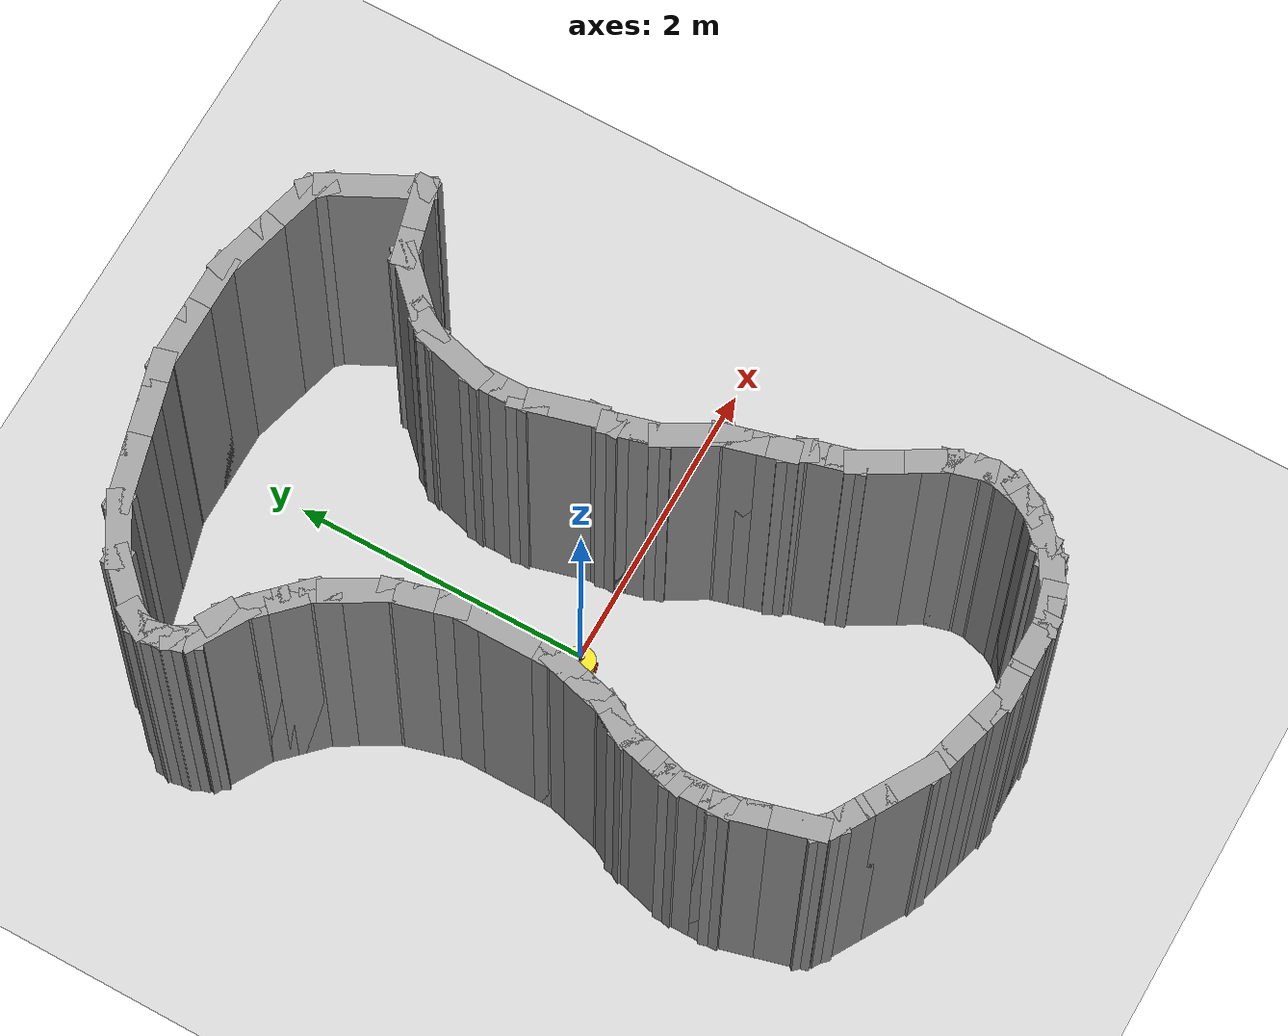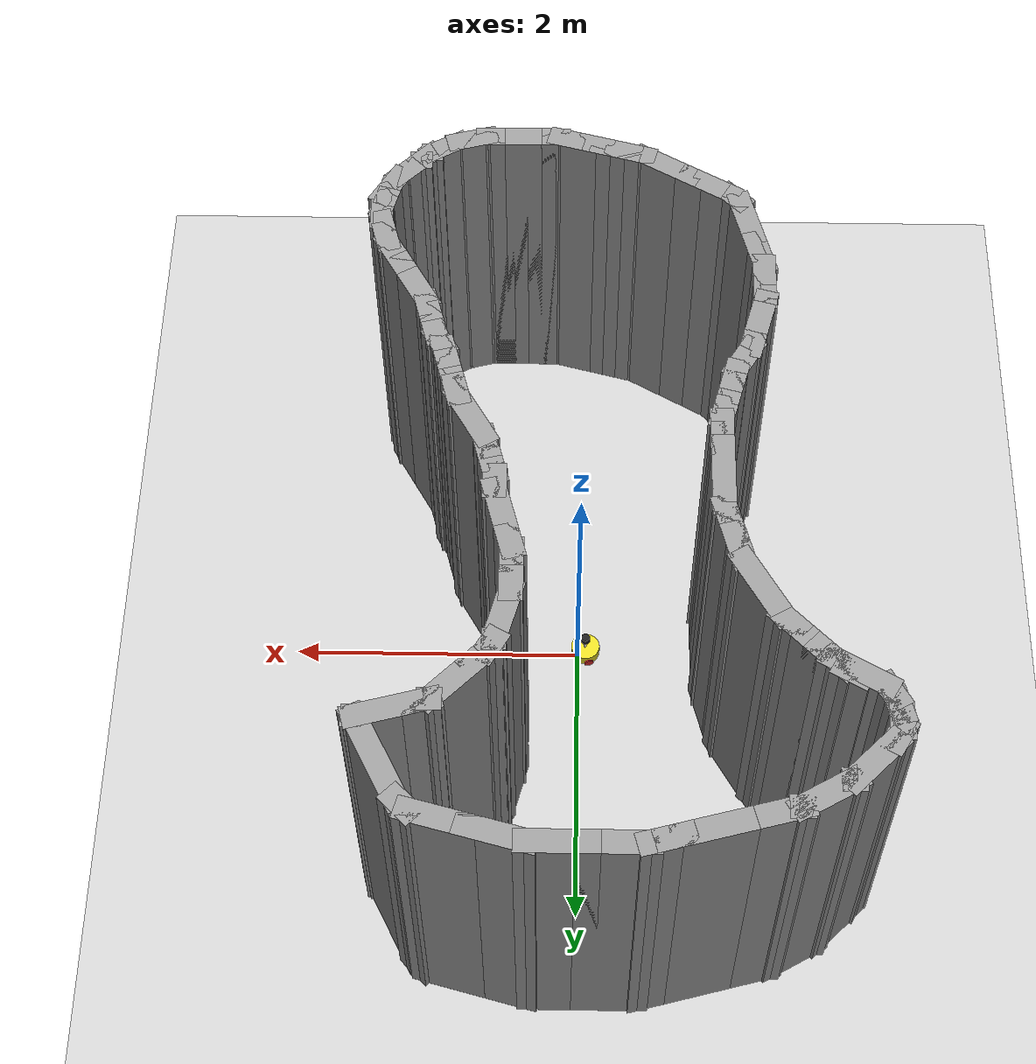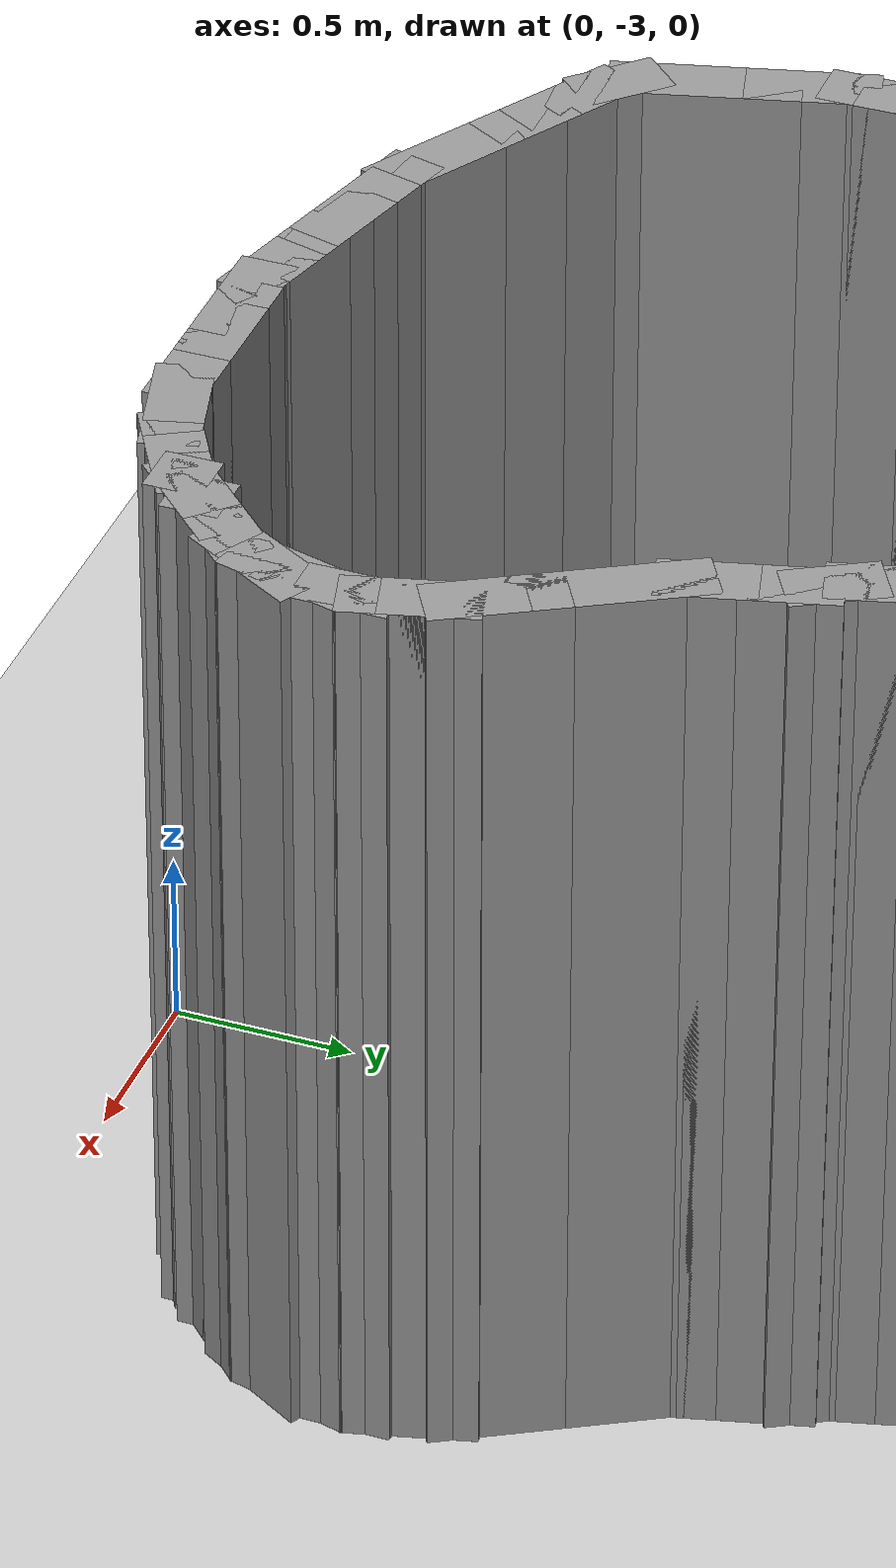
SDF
<sdf version="1.7">
 <world name="default">
  <light name="sun" type="directional">
   <pose>0 0 10 0 -0 0</pose>
   <diffuse>0.8 0.8 0.8 1</diffuse>
   <specular>0.2 0.2 0.2 1</specular>
   <attenuation>
    <range>1000</range>
    <constant>0.9</constant>
    <linear>0.01</linear>
    <quadratic>0.001</quadratic>
   </attenuation>
   <direction>-0.5 0.1 -0.9</direction>
   <spot><inner_angle>0</inner_angle><outer_angle>0</outer_angle><falloff>0</falloff></spot>
  </light>
  <model name="ground_plane">
   <static>1</static>
   <link name="link">
    <collision name="collision">
     <geometry><plane><normal>0 0 1</normal><size>100 100</size></plane></geometry>
     <surface>
      <contact><collide_bitmask>65535</collide_bitmask></contact>
      <friction><ode><mu>100</mu><mu2>50</mu2></ode></friction>
     </surface>
    </collision>
    <visual name="visual">
     <cast_shadows>0</cast_shadows>
     <geometry><plane><normal>0 0 1</normal><size>100 100</size></plane></geometry>
     <material>
      <script><uri>file://media/materials/scripts/gazebo.material</uri><name>Gazebo/Grey</name></script>
     </material>
    </visual>
   </link>
  </model>
  <gravity>0 0 -9.8</gravity>
  <magnetic_field>6e-06 2.3e-05 -4.2e-05</magnetic_field>
  <atmosphere type="adiabatic"/>
  <physics type="ode">
   <max_step_size>0.001</max_step_size>
   <real_time_factor>1</real_time_factor>
   <real_time_update_rate>1000</real_time_update_rate>
  </physics>
  <scene><ambient>0.4 0.4 0.4 1</ambient><background>0.7 0.7 0.7 1</background><shadows>1</shadows></scene>
  <spherical_coordinates>
   <surface_model>EARTH_WGS84</surface_model>
   <latitude_deg>0</latitude_deg>
   <longitude_deg>0</longitude_deg>
   <elevation>0</elevation>
   <heading_deg>0</heading_deg>
  </spherical_coordinates>
  <model name="pool_robot">
   <link name="base_footprint">
    <inertial>
     <pose>0.00125 0 0.078945 0 -0 0</pose>
     <mass>0.64</mass>
     <inertia>
      <ixx>0.00325137</ixx>
      <ixy>0</ixy>
      <ixz>-2.28438e-05</ixz>
      <iyy>0.00331437</iyy>
      <iyz>0</iyz>
      <izz>0.00261021</izz>
     </inertia>
    </inertial>
    <collision name="base_footprint_fixed_joint_lump__base_link_collision">
     <pose>0 0 0.055 0 -0 0</pose>
     <geometry><cylinder><length>0.08</length><radius>0.1</radius></cylinder></geometry>
    </collision>
    <collision name="base_footprint_fixed_joint_lump__camera_collision_1">
     <pose>0.08 0 0.1075 0 -0 0</pose>
     <geometry><box><size>0.01 0.025 0.025</size></box></geometry>
    </collision>
    <collision name="base_footprint_fixed_joint_lump__imu_collision_2">
     <pose>0 0 0.055 0 -0 0</pose>
     <geometry><box><size>0.01 0.01 0.01</size></box></geometry>
    </collision>
    <collision name="base_footprint_fixed_joint_lump__support_collision_3">
     <pose>0 0 0.095 0 -0 0</pose>
     <geometry><cylinder><length>0.15</length><radius>0.01</radius></cylinder></geometry>
    </collision>
    <collision name="base_footprint_fixed_joint_lump__laser_collision_4">
     <pose>0 0 0.195 0 -0 0</pose>
     <geometry><cylinder><length>0.05</length><radius>0.03</radius></cylinder></geometry>
    </collision>
    <visual name="base_footprint_visual"><geometry><sphere><radius>0.001</radius></sphere></geometry></visual>
    <visual name="base_footprint_fixed_joint_lump__base_link_visual_1">
     <pose>0 0 0.055 0 -0 0</pose>
     <geometry><cylinder><length>0.08</length><radius>0.1</radius></cylinder></geometry>
     <material>
      <script><name>Gazebo/Yellow</name><uri>file://media/materials/scripts/gazebo.material</uri></script>
     </material>
    </visual>
    <visual name="base_footprint_fixed_joint_lump__camera_visual_2">
     <pose>0.08 0 0.1075 0 -0 0</pose>
     <geometry><box><size>0.01 0.025 0.025</size></box></geometry>
     <material>
      <script><name>Gazebo/Blue</name><uri>file://media/materials/scripts/gazebo.material</uri></script>
     </material>
    </visual>
    <visual name="base_footprint_fixed_joint_lump__imu_visual_3">
     <pose>0 0 0.055 0 -0 0</pose>
     <geometry><box><size>0.01 0.01 0.01</size></box></geometry>
     <material>
      <script><name>Gazebo/Red</name><uri>file://media/materials/scripts/gazebo.material</uri></script>
     </material>
    </visual>
    <visual name="base_footprint_fixed_joint_lump__support_visual_4">
     <pose>0 0 0.095 0 -0 0</pose>
     <geometry><cylinder><length>0.15</length><radius>0.01</radius></cylinder></geometry>
     <material>
      <script><name>Gazebo/White</name><uri>file://media/materials/scripts/gazebo.material</uri></script>
     </material>
    </visual>
    <visual name="base_footprint_fixed_joint_lump__laser_visual_5">
     <pose>0 0 0.195 0 -0 0</pose>
     <geometry><cylinder><length>0.05</length><radius>0.03</radius></cylinder></geometry>
     <material>
      <script><name>Gazebo/Black</name><uri>file://media/materials/scripts/gazebo.material</uri></script>
     </material>
    </visual>
    <sensor name="imu_sensor" type="imu">
     <always_on>1</always_on>
     <update_rate>100</update_rate>
     <visualize>1</visualize>
     <topic>__default_topic__</topic>
     <plugin name="imu_plugin" filename="libgazebo_ros_imu_sensor.so">
      <topicName>imu</topicName>
      <bodyName>imu</bodyName>
      <updateRateHZ>100.0</updateRateHZ>
      <gaussianNoise>0.0</gaussianNoise>
      <xyzOffset>0 0 0</xyzOffset>
      <rpyOffset>0 0 0</rpyOffset>
      <frameName>imu</frameName>
      <robotNamespace>/</robotNamespace>
     </plugin>
     <pose>0 0 0.055 0 -0 0</pose>
    </sensor>
    <sensor name="rplidar" type="ray">
     <visualize>1</visualize>
     <update_rate>5.5</update_rate>
     <ray>
      <scan>
       <horizontal>
        <samples>360</samples>
        <resolution>1</resolution>
        <min_angle>0</min_angle>
        <max_angle>360</max_angle>
       </horizontal>
       <vertical><samples>1</samples><min_angle>0</min_angle><max_angle>0</max_angle></vertical>
      </scan>
      <range><min>0.1</min><max>3</max><resolution>0.01</resolution></range>
      <noise><type>gaussian</type><mean>0</mean><stddev>0.01</stddev></noise>
     </ray>
     <plugin name="gazebo_rplidar" filename="libgazebo_ros_laser.so">
      <topicName>/scan</topicName>
      <frameName>laser</frameName>
      <robotNamespace>/</robotNamespace>
     </plugin>
     <pose>0 0 0.195 0 -0 0</pose>
    </sensor>
   </link>
   <joint name="back_wheel2base_link" type="revolute">
    <pose relative_to="base_footprint">-0.0925 0 0.0075 0 -0 0</pose>
    <parent>base_footprint</parent>
    <child>back_wheel</child>
    <axis>
     <xyz>1 1 1</xyz>
     <limit><lower>-1e+16</lower><upper>1e+16</upper></limit>
     <dynamics><spring_reference>0</spring_reference><spring_stiffness>0</spring_stiffness></dynamics>
    </axis>
   </joint>
   <link name="back_wheel">
    <pose relative_to="back_wheel2base_link">0 0 0 0 -0 0</pose>
    <inertial>
     <mass>0.03</mass>
     <inertia>
      <ixx>6.75e-07</ixx>
      <ixy>0</ixy>
      <ixz>0</ixz>
      <iyy>6.75e-07</iyy>
      <iyz>0</iyz>
      <izz>6.75e-07</izz>
     </inertia>
    </inertial>
    <collision name="back_wheel_collision">
     <geometry><sphere><radius>0.0075</radius></sphere></geometry>
    </collision>
    <visual name="back_wheel_visual">
     <geometry><sphere><radius>0.0075</radius></sphere></geometry>
     <material>
      <script><name>Gazebo/Red</name><uri>file://media/materials/scripts/gazebo.material</uri></script>
     </material>
    </visual>
   </link>
   <joint name="front_wheel2base_link" type="revolute">
    <pose relative_to="base_footprint">0.0925 0 0.0075 0 -0 0</pose>
    <parent>base_footprint</parent>
    <child>front_wheel</child>
    <axis>
     <xyz>1 1 1</xyz>
     <limit><lower>-1e+16</lower><upper>1e+16</upper></limit>
     <dynamics><spring_reference>0</spring_reference><spring_stiffness>0</spring_stiffness></dynamics>
    </axis>
   </joint>
   <link name="front_wheel">
    <pose relative_to="front_wheel2base_link">0 0 0 0 -0 0</pose>
    <inertial>
     <mass>0.03</mass>
     <inertia>
      <ixx>6.75e-07</ixx>
      <ixy>0</ixy>
      <ixz>0</ixz>
      <iyy>6.75e-07</iyy>
      <iyz>0</iyz>
      <izz>6.75e-07</izz>
     </inertia>
    </inertial>
    <collision name="front_wheel_collision">
     <geometry><sphere><radius>0.0075</radius></sphere></geometry>
    </collision>
    <visual name="front_wheel_visual">
     <geometry><sphere><radius>0.0075</radius></sphere></geometry>
     <material>
      <script><name>Gazebo/Red</name><uri>file://media/materials/scripts/gazebo.material</uri></script>
     </material>
    </visual>
   </link>
   <joint name="left_wheel2base_link" type="revolute">
    <pose relative_to="base_footprint">0 0.1 0.0325 0 -0 0</pose>
    <parent>base_footprint</parent>
    <child>left_wheel</child>
    <axis>
     <xyz>0 1 0</xyz>
     <limit><lower>-1e+16</lower><upper>1e+16</upper></limit>
     <dynamics><spring_reference>0</spring_reference><spring_stiffness>0</spring_stiffness></dynamics>
    </axis>
   </joint>
   <link name="left_wheel">
    <pose relative_to="left_wheel2base_link">0 0 0 0 -0 0</pose>
    <inertial>
     <mass>0.05</mass>
     <inertia>
      <ixx>1.41406e-05</ixx>
      <ixy>0</ixy>
      <ixz>0</ixz>
      <iyy>1.41406e-05</iyy>
      <iyz>0</iyz>
      <izz>2.64063e-05</izz>
     </inertia>
    </inertial>
    <collision name="left_wheel_collision">
     <pose>0 0 0 1.5708 -0 0</pose>
     <geometry><cylinder><length>0.015</length><radius>0.0325</radius></cylinder></geometry>
    </collision>
    <visual name="left_wheel_visual">
     <pose>0 0 0 1.5708 -0 0</pose>
     <geometry><cylinder><length>0.015</length><radius>0.0325</radius></cylinder></geometry>
     <material>
      <script><name>Gazebo/Red</name><uri>file://media/materials/scripts/gazebo.material</uri></script>
     </material>
    </visual>
   </link>
   <joint name="right_wheel2base_link" type="revolute">
    <pose relative_to="base_footprint">0 -0.1 0.0325 0 -0 0</pose>
    <parent>base_footprint</parent>
    <child>right_wheel</child>
    <axis>
     <xyz>0 1 0</xyz>
     <limit><lower>-1e+16</lower><upper>1e+16</upper></limit>
     <dynamics><spring_reference>0</spring_reference><spring_stiffness>0</spring_stiffness></dynamics>
    </axis>
   </joint>
   <link name="right_wheel">
    <pose relative_to="right_wheel2base_link">0 0 0 0 -0 0</pose>
    <inertial>
     <mass>0.05</mass>
     <inertia>
      <ixx>1.41406e-05</ixx>
      <ixy>0</ixy>
      <ixz>0</ixz>
      <iyy>1.41406e-05</iyy>
      <iyz>0</iyz>
      <izz>2.64063e-05</izz>
     </inertia>
    </inertial>
    <collision name="right_wheel_collision">
     <pose>0 0 0 1.5708 -0 0</pose>
     <geometry><cylinder><length>0.015</length><radius>0.0325</radius></cylinder></geometry>
    </collision>
    <visual name="right_wheel_visual">
     <pose>0 0 0 1.5708 -0 0</pose>
     <geometry><cylinder><length>0.015</length><radius>0.0325</radius></cylinder></geometry>
     <material>
      <script><name>Gazebo/Red</name><uri>file://media/materials/scripts/gazebo.material</uri></script>
     </material>
    </visual>
   </link>
   <plugin name="differential_drive_controller" filename="libgazebo_ros_diff_drive.so">
    <rosDebugLevel>Debug</rosDebugLevel>
    <publishWheelTF>1</publishWheelTF>
    <robotNamespace>/</robotNamespace>
    <publishTf>1</publishTf>
    <publishWheelJointState>1</publishWheelJointState>
    <alwaysOn>1</alwaysOn>
    <updateRate>100.0</updateRate>
    <legacyMode>1</legacyMode>
    <leftJoint>left_wheel2base_link</leftJoint>
    <rightJoint>right_wheel2base_link</rightJoint>
    <wheelSeparation>0.2</wheelSeparation>
    <wheelDiameter>0.065</wheelDiameter>
    <broadcastTF>1</broadcastTF>
    <wheelTorque>30</wheelTorque>
    <wheelAcceleration>1.8</wheelAcceleration>
    <commandTopic>cmd_vel</commandTopic>
    <odometryFrame>odom</odometryFrame>
    <odometryTopic>odom</odometryTopic>
    <robotBaseFrame>base_footprint</robotBaseFrame>
   </plugin>
   <frame name="camera2base_link" attached_to="base_link"><pose>0.08 0 0.0525 0 -0 0</pose></frame>
   <frame name="camera" attached_to="camera2base_link"/>
   <frame name="imu2base_link" attached_to="base_link"/>
   <frame name="imu" attached_to="imu2base_link"/>
   <frame name="laser2support" attached_to="support"><pose>0 0 0.1 0 -0 0</pose></frame>
   <frame name="laser" attached_to="laser2support"/>
   <frame name="support2base_link" attached_to="base_link"><pose>0 0 0.04 0 -0 0</pose></frame>
   <frame name="support" attached_to="support2base_link"/>
   <frame name="base_link2base_footprint" attached_to="base_footprint"><pose>0 0 0.055 0 -0 0</pose></frame>
   <frame name="base_link" attached_to="base_link2base_footprint"/>
   <pose>-0.053591 -0.025871 0 0 -0 0.265443</pose>
  </model>
  <model name="spoll2">
   <pose>1.26645 -0.043503 0 0 -0 0</pose>
   <link name="Wall_222">
    <collision name="Wall_222_Collision">
     <geometry><box><size>0.25 0.15 2.5</size></box></geometry>
     <pose>0 0 1.25 0 -0 0</pose>
    </collision>
    <visual name="Wall_222_Visual">
     <pose>0 0 1.25 0 -0 0</pose>
     <geometry><box><size>0.25 0.15 2.5</size></box></geometry>
     <material>
      <script><uri>file://media/materials/scripts/gazebo.material</uri><name>Gazebo/Grey</name></script>
      <ambient>1 1 1 1</ambient>
     </material>
     <meta><layer>0</layer></meta>
    </visual>
    <pose>-2.8675 1.51416 0 0 -0 -0.523599</pose>
   </link>
   <link name="Wall_223">
    <collision name="Wall_223_Collision">
     <geometry><box><size>0.25 0.15 2.5</size></box></geometry>
     <pose>0 0 1.25 0 -0 0</pose>
    </collision>
    <visual name="Wall_223_Visual">
     <pose>0 0 1.25 0 -0 0</pose>
     <geometry><box><size>0.25 0.15 2.5</size></box></geometry>
     <material>
      <script><uri>file://media/materials/scripts/gazebo.material</uri><name>Gazebo/Grey</name></script>
      <ambient>1 1 1 1</ambient>
     </material>
     <meta><layer>0</layer></meta>
    </visual>
    <pose>-2.78885 1.45381 0 0 -0 -0.785398</pose>
   </link>
   <link name="Wall_224">
    <collision name="Wall_224_Collision">
     <geometry><box><size>0.25 0.15 2.5</size></box></geometry>
     <pose>0 0 1.25 0 -0 0</pose>
    </collision>
    <visual name="Wall_224_Visual">
     <pose>0 0 1.25 0 -0 0</pose>
     <geometry><box><size>0.25 0.15 2.5</size></box></geometry>
     <material>
      <script><uri>file://media/materials/scripts/gazebo.material</uri><name>Gazebo/Grey</name></script>
      <ambient>1 1 1 1</ambient>
     </material>
     <meta><layer>0</layer></meta>
    </visual>
    <pose>-2.71814 1.3831 0 0 -0 -0.785398</pose>
   </link>
   <link name="Wall_225">
    <collision name="Wall_225_Collision">
     <geometry><box><size>0.25 0.15 2.5</size></box></geometry>
     <pose>0 0 1.25 0 -0 0</pose>
    </collision>
    <visual name="Wall_225_Visual">
     <pose>0 0 1.25 0 -0 0</pose>
     <geometry><box><size>0.25 0.15 2.5</size></box></geometry>
     <material>
      <script><uri>file://media/materials/scripts/gazebo.material</uri><name>Gazebo/Grey</name></script>
      <ambient>1 1 1 1</ambient>
     </material>
     <meta><layer>0</layer></meta>
    </visual>
    <pose>-2.64743 1.31239 0 0 -0 -0.785398</pose>
   </link>
   <link name="Wall_226">
    <collision name="Wall_226_Collision">
     <geometry><box><size>0.25 0.15 2.5</size></box></geometry>
     <pose>0 0 1.25 0 -0 0</pose>
    </collision>
    <visual name="Wall_226_Visual">
     <pose>0 0 1.25 0 -0 0</pose>
     <geometry><box><size>0.25 0.15 2.5</size></box></geometry>
     <material>
      <script><uri>file://media/materials/scripts/gazebo.material</uri><name>Gazebo/Grey</name></script>
      <ambient>1 1 1 1</ambient>
     </material>
     <meta><layer>0</layer></meta>
    </visual>
    <pose>-2.57672 1.24168 0 0 -0 -0.785398</pose>
   </link>
   <link name="Wall_227">
    <collision name="Wall_227_Collision">
     <geometry><box><size>0.25 0.15 2.5</size></box></geometry>
     <pose>0 0 1.25 0 -0 0</pose>
    </collision>
    <visual name="Wall_227_Visual">
     <pose>0 0 1.25 0 -0 0</pose>
     <geometry><box><size>0.25 0.15 2.5</size></box></geometry>
     <material>
      <script><uri>file://media/materials/scripts/gazebo.material</uri><name>Gazebo/Grey</name></script>
      <ambient>1 1 1 1</ambient>
     </material>
     <meta><layer>0</layer></meta>
    </visual>
    <pose>-2.50601 1.17097 0 0 -0 -0.785398</pose>
   </link>
   <link name="Wall_228">
    <collision name="Wall_228_Collision">
     <geometry><box><size>0.25 0.15 2.5</size></box></geometry>
     <pose>0 0 1.25 0 -0 0</pose>
    </collision>
    <visual name="Wall_228_Visual">
     <pose>0 0 1.25 0 -0 0</pose>
     <geometry><box><size>0.25 0.15 2.5</size></box></geometry>
     <material>
      <script><uri>file://media/materials/scripts/gazebo.material</uri><name>Gazebo/Grey</name></script>
      <ambient>1 1 1 1</ambient>
     </material>
     <meta><layer>0</layer></meta>
    </visual>
    <pose>-2.44565 1.09231 0 0 -0 -1.0472</pose>
   </link>
   <link name="Wall_229">
    <collision name="Wall_229_Collision">
     <geometry><box><size>0.5 0.15 2.5</size></box></geometry>
     <pose>0 0 1.25 0 -0 0</pose>
    </collision>
    <visual name="Wall_229_Visual">
     <pose>0 0 1.25 0 -0 0</pose>
     <geometry><box><size>0.5 0.15 2.5</size></box></geometry>
     <material>
      <script><uri>file://media/materials/scripts/gazebo.material</uri><name>Gazebo/Grey</name></script>
      <ambient>1 1 1 1</ambient>
     </material>
     <meta><layer>0</layer></meta>
    </visual>
    <pose>-2.33315 0.897455 0 0 -0 -1.0472</pose>
   </link>
   <link name="Wall_230">
    <collision name="Wall_230_Collision">
     <geometry><box><size>0.25 0.15 2.5</size></box></geometry>
     <pose>0 0 1.25 0 -0 0</pose>
    </collision>
    <visual name="Wall_230_Visual">
     <pose>0 0 1.25 0 -0 0</pose>
     <geometry><box><size>0.25 0.15 2.5</size></box></geometry>
     <material>
      <script><uri>file://media/materials/scripts/gazebo.material</uri><name>Gazebo/Grey</name></script>
      <ambient>1 1 1 1</ambient>
     </material>
     <meta><layer>0</layer></meta>
    </visual>
    <pose>-2.23271 0.697604 0 0 -0 -1.309</pose>
   </link>
   <link name="Wall_231">
    <collision name="Wall_231_Collision">
     <geometry><box><size>0.25 0.15 2.5</size></box></geometry>
     <pose>0 0 1.25 0 -0 0</pose>
    </collision>
    <visual name="Wall_231_Visual">
     <pose>0 0 1.25 0 -0 0</pose>
     <geometry><box><size>0.25 0.15 2.5</size></box></geometry>
     <material>
      <script><uri>file://media/materials/scripts/gazebo.material</uri><name>Gazebo/Grey</name></script>
      <ambient>1 1 1 1</ambient>
     </material>
     <meta><layer>0</layer></meta>
    </visual>
    <pose>-2.20683 0.601012 0 0 -0 -1.309</pose>
   </link>
   <link name="Wall_232">
    <collision name="Wall_232_Collision">
     <geometry><box><size>0.25 0.15 2.5</size></box></geometry>
     <pose>0 0 1.25 0 -0 0</pose>
    </collision>
    <visual name="Wall_232_Visual">
     <pose>0 0 1.25 0 -0 0</pose>
     <geometry><box><size>0.25 0.15 2.5</size></box></geometry>
     <material>
      <script><uri>file://media/materials/scripts/gazebo.material</uri><name>Gazebo/Grey</name></script>
      <ambient>1 1 1 1</ambient>
     </material>
     <meta><layer>0</layer></meta>
    </visual>
    <pose>-2.18094 0.504419 0 0 -0 -1.309</pose>
   </link>
   <link name="Wall_233">
    <collision name="Wall_233_Collision">
     <geometry><box><size>0.25 0.15 2.5</size></box></geometry>
     <pose>0 0 1.25 0 -0 0</pose>
    </collision>
    <visual name="Wall_233_Visual">
     <pose>0 0 1.25 0 -0 0</pose>
     <geometry><box><size>0.25 0.15 2.5</size></box></geometry>
     <material>
      <script><uri>file://media/materials/scripts/gazebo.material</uri><name>Gazebo/Grey</name></script>
      <ambient>1 1 1 1</ambient>
     </material>
     <meta><layer>0</layer></meta>
    </visual>
    <pose>-2.15506 0.407827 0 0 -0 -1.309</pose>
   </link>
   <link name="Wall_234">
    <collision name="Wall_234_Collision">
     <geometry><box><size>0.25 0.15 2.5</size></box></geometry>
     <pose>0 0 1.25 0 -0 0</pose>
    </collision>
    <visual name="Wall_234_Visual">
     <pose>0 0 1.25 0 -0 0</pose>
     <geometry><box><size>0.25 0.15 2.5</size></box></geometry>
     <material>
      <script><uri>file://media/materials/scripts/gazebo.material</uri><name>Gazebo/Grey</name></script>
      <ambient>1 1 1 1</ambient>
     </material>
     <meta><layer>0</layer></meta>
    </visual>
    <pose>-2.14212 0.30953 0 0 -0 -1.5708</pose>
   </link>
   <link name="Wall_235">
    <collision name="Wall_235_Collision">
     <geometry><box><size>0.5 0.15 2.5</size></box></geometry>
     <pose>0 0 1.25 0 -0 0</pose>
    </collision>
    <visual name="Wall_235_Visual">
     <pose>0 0 1.25 0 -0 0</pose>
     <geometry><box><size>0.5 0.15 2.5</size></box></geometry>
     <material>
      <script><uri>file://media/materials/scripts/gazebo.material</uri><name>Gazebo/Grey</name></script>
      <ambient>1 1 1 1</ambient>
     </material>
     <meta><layer>0</layer></meta>
    </visual>
    <pose>-2.14212 0.08453 0 0 -0 -1.5708</pose>
   </link>
   <link name="Wall_236">
    <collision name="Wall_236_Collision">
     <geometry><box><size>0.25 0.15 2.5</size></box></geometry>
     <pose>0 0 1.25 0 -0 0</pose>
    </collision>
    <visual name="Wall_236_Visual">
     <pose>0 0 1.25 0 -0 0</pose>
     <geometry><box><size>0.25 0.15 2.5</size></box></geometry>
     <material>
      <script><uri>file://media/materials/scripts/gazebo.material</uri><name>Gazebo/Grey</name></script>
      <ambient>1 1 1 1</ambient>
     </material>
     <meta><layer>0</layer></meta>
    </visual>
    <pose>-2.14212 -0.14047 0 0 -0 -1.5708</pose>
   </link>
   <link name="Wall_237">
    <collision name="Wall_237_Collision">
     <geometry><box><size>0.25 0.15 2.5</size></box></geometry>
     <pose>0 0 1.25 0 -0 0</pose>
    </collision>
    <visual name="Wall_237_Visual">
     <pose>0 0 1.25 0 -0 0</pose>
     <geometry><box><size>0.25 0.15 2.5</size></box></geometry>
     <material>
      <script><uri>file://media/materials/scripts/gazebo.material</uri><name>Gazebo/Grey</name></script>
      <ambient>1 1 1 1</ambient>
     </material>
     <meta><layer>0</layer></meta>
    </visual>
    <pose>-2.14212 -0.24047 0 0 -0 -1.5708</pose>
   </link>
   <link name="Wall_238">
    <collision name="Wall_238_Collision">
     <geometry><box><size>0.25 0.15 2.5</size></box></geometry>
     <pose>0 0 1.25 0 -0 0</pose>
    </collision>
    <visual name="Wall_238_Visual">
     <pose>0 0 1.25 0 -0 0</pose>
     <geometry><box><size>0.25 0.15 2.5</size></box></geometry>
     <material>
      <script><uri>file://media/materials/scripts/gazebo.material</uri><name>Gazebo/Grey</name></script>
      <ambient>1 1 1 1</ambient>
     </material>
     <meta><layer>0</layer></meta>
    </visual>
    <pose>-2.15506 -0.338766 0 0 -0 -1.8326</pose>
   </link>
   <link name="Wall_239">
    <collision name="Wall_239_Collision">
     <geometry><box><size>0.25 0.15 2.5</size></box></geometry>
     <pose>0 0 1.25 0 -0 0</pose>
    </collision>
    <visual name="Wall_239_Visual">
     <pose>0 0 1.25 0 -0 0</pose>
     <geometry><box><size>0.25 0.15 2.5</size></box></geometry>
     <material>
      <script><uri>file://media/materials/scripts/gazebo.material</uri><name>Gazebo/Grey</name></script>
      <ambient>1 1 1 1</ambient>
     </material>
     <meta><layer>0</layer></meta>
    </visual>
    <pose>-2.18094 -0.435359 0 0 -0 -1.8326</pose>
   </link>
   <link name="Wall_240">
    <collision name="Wall_240_Collision">
     <geometry><box><size>0.25 0.15 2.5</size></box></geometry>
     <pose>0 0 1.25 0 -0 0</pose>
    </collision>
    <visual name="Wall_240_Visual">
     <pose>0 0 1.25 0 -0 0</pose>
     <geometry><box><size>0.25 0.15 2.5</size></box></geometry>
     <material>
      <script><uri>file://media/materials/scripts/gazebo.material</uri><name>Gazebo/Grey</name></script>
      <ambient>1 1 1 1</ambient>
     </material>
     <meta><layer>0</layer></meta>
    </visual>
    <pose>-2.20683 -0.531951 0 0 -0 -1.8326</pose>
   </link>
   <link name="Wall_241">
    <collision name="Wall_241_Collision">
     <geometry><box><size>0.25 0.15 2.5</size></box></geometry>
     <pose>0 0 1.25 0 -0 0</pose>
    </collision>
    <visual name="Wall_241_Visual">
     <pose>0 0 1.25 0 -0 0</pose>
     <geometry><box><size>0.25 0.15 2.5</size></box></geometry>
     <material>
      <script><uri>file://media/materials/scripts/gazebo.material</uri><name>Gazebo/Grey</name></script>
      <ambient>1 1 1 1</ambient>
     </material>
     <meta><layer>0</layer></meta>
    </visual>
    <pose>-2.23271 -0.628544 0 0 -0 -1.8326</pose>
   </link>
   <link name="Wall_242">
    <collision name="Wall_242_Collision">
     <geometry><box><size>0.25 0.15 2.5</size></box></geometry>
     <pose>0 0 1.25 0 -0 0</pose>
    </collision>
    <visual name="Wall_242_Visual">
     <pose>0 0 1.25 0 -0 0</pose>
     <geometry><box><size>0.25 0.15 2.5</size></box></geometry>
     <material>
      <script><uri>file://media/materials/scripts/gazebo.material</uri><name>Gazebo/Grey</name></script>
      <ambient>1 1 1 1</ambient>
     </material>
     <meta><layer>0</layer></meta>
    </visual>
    <pose>-2.27065 -0.720141 0 0 -0 -2.0944</pose>
   </link>
   <link name="Wall_243">
    <collision name="Wall_243_Collision">
     <geometry><box><size>0.25 0.15 2.5</size></box></geometry>
     <pose>0 0 1.25 0 -0 0</pose>
    </collision>
    <visual name="Wall_243_Visual">
     <pose>0 0 1.25 0 -0 0</pose>
     <geometry><box><size>0.25 0.15 2.5</size></box></geometry>
     <material>
      <script><uri>file://media/materials/scripts/gazebo.material</uri><name>Gazebo/Grey</name></script>
      <ambient>1 1 1 1</ambient>
     </material>
     <meta><layer>0</layer></meta>
    </visual>
    <pose>-2.32065 -0.806744 0 0 -0 -2.0944</pose>
   </link>
   <link name="Wall_244">
    <collision name="Wall_244_Collision">
     <geometry><box><size>0.25 0.15 2.5</size></box></geometry>
     <pose>0 0 1.25 0 -0 0</pose>
    </collision>
    <visual name="Wall_244_Visual">
     <pose>0 0 1.25 0 -0 0</pose>
     <geometry><box><size>0.25 0.15 2.5</size></box></geometry>
     <material>
      <script><uri>file://media/materials/scripts/gazebo.material</uri><name>Gazebo/Grey</name></script>
      <ambient>1 1 1 1</ambient>
     </material>
     <meta><layer>0</layer></meta>
    </visual>
    <pose>-2.35859 -0.898342 0 0 -0 -1.8326</pose>
   </link>
   <link name="Wall_245">
    <collision name="Wall_245_Collision">
     <geometry><box><size>0.25 0.15 2.5</size></box></geometry>
     <pose>0 0 1.25 0 -0 0</pose>
    </collision>
    <visual name="Wall_245_Visual">
     <pose>0 0 1.25 0 -0 0</pose>
     <geometry><box><size>0.25 0.15 2.5</size></box></geometry>
     <material>
      <script><uri>file://media/materials/scripts/gazebo.material</uri><name>Gazebo/Grey</name></script>
      <ambient>1 1 1 1</ambient>
     </material>
     <meta><layer>0</layer></meta>
    </visual>
    <pose>-2.38447 -0.994934 0 0 -0 -1.8326</pose>
   </link>
   <link name="Wall_246">
    <collision name="Wall_246_Collision">
     <geometry><box><size>0.25 0.15 2.5</size></box></geometry>
     <pose>0 0 1.25 0 -0 0</pose>
    </collision>
    <visual name="Wall_246_Visual">
     <pose>0 0 1.25 0 -0 0</pose>
     <geometry><box><size>0.25 0.15 2.5</size></box></geometry>
     <material>
      <script><uri>file://media/materials/scripts/gazebo.material</uri><name>Gazebo/Grey</name></script>
      <ambient>1 1 1 1</ambient>
     </material>
     <meta><layer>0</layer></meta>
    </visual>
    <pose>-2.41036 -1.09153 0 0 -0 -1.8326</pose>
   </link>
   <link name="Wall_247">
    <collision name="Wall_247_Collision">
     <geometry><box><size>0.25 0.15 2.5</size></box></geometry>
     <pose>0 0 1.25 0 -0 0</pose>
    </collision>
    <visual name="Wall_247_Visual">
     <pose>0 0 1.25 0 -0 0</pose>
     <geometry><box><size>0.25 0.15 2.5</size></box></geometry>
     <material>
      <script><uri>file://media/materials/scripts/gazebo.material</uri><name>Gazebo/Grey</name></script>
      <ambient>1 1 1 1</ambient>
     </material>
     <meta><layer>0</layer></meta>
    </visual>
    <pose>-2.43624 -1.18812 0 0 -0 -1.8326</pose>
   </link>
   <link name="Wall_248">
    <collision name="Wall_248_Collision">
     <geometry><box><size>0.25 0.15 2.5</size></box></geometry>
     <pose>0 0 1.25 0 -0 0</pose>
    </collision>
    <visual name="Wall_248_Visual">
     <pose>0 0 1.25 0 -0 0</pose>
     <geometry><box><size>0.25 0.15 2.5</size></box></geometry>
     <material>
      <script><uri>file://media/materials/scripts/gazebo.material</uri><name>Gazebo/Grey</name></script>
      <ambient>1 1 1 1</ambient>
     </material>
     <meta><layer>0</layer></meta>
    </visual>
    <pose>-2.44918 -1.28642 0 0 -0 -1.5708</pose>
   </link>
   <link name="Wall_249">
    <collision name="Wall_249_Collision">
     <geometry><box><size>0.25 0.15 2.5</size></box></geometry>
     <pose>0 0 1.25 0 -0 0</pose>
    </collision>
    <visual name="Wall_249_Visual">
     <pose>0 0 1.25 0 -0 0</pose>
     <geometry><box><size>0.25 0.15 2.5</size></box></geometry>
     <material>
      <script><uri>file://media/materials/scripts/gazebo.material</uri><name>Gazebo/Grey</name></script>
      <ambient>1 1 1 1</ambient>
     </material>
     <meta><layer>0</layer></meta>
    </visual>
    <pose>-2.44918 -1.38642 0 0 -0 -1.5708</pose>
   </link>
   <link name="Wall_250">
    <collision name="Wall_250_Collision">
     <geometry><box><size>0.25 0.15 2.5</size></box></geometry>
     <pose>0 0 1.25 0 -0 0</pose>
    </collision>
    <visual name="Wall_250_Visual">
     <pose>0 0 1.25 0 -0 0</pose>
     <geometry><box><size>0.25 0.15 2.5</size></box></geometry>
     <material>
      <script><uri>file://media/materials/scripts/gazebo.material</uri><name>Gazebo/Grey</name></script>
      <ambient>1 1 1 1</ambient>
     </material>
     <meta><layer>0</layer></meta>
    </visual>
    <pose>-2.44918 -1.48642 0 0 -0 -1.5708</pose>
   </link>
   <link name="Wall_251">
    <collision name="Wall_251_Collision">
     <geometry><box><size>0.25 0.15 2.5</size></box></geometry>
     <pose>0 0 1.25 0 -0 0</pose>
    </collision>
    <visual name="Wall_251_Visual">
     <pose>0 0 1.25 0 -0 0</pose>
     <geometry><box><size>0.25 0.15 2.5</size></box></geometry>
     <material>
      <script><uri>file://media/materials/scripts/gazebo.material</uri><name>Gazebo/Grey</name></script>
      <ambient>1 1 1 1</ambient>
     </material>
     <meta><layer>0</layer></meta>
    </visual>
    <pose>-2.43624 -1.58471 0 0 -0 -1.309</pose>
   </link>
   <link name="Wall_252">
    <collision name="Wall_252_Collision">
     <geometry><box><size>0.25 0.15 2.5</size></box></geometry>
     <pose>0 0 1.25 0 -0 0</pose>
    </collision>
    <visual name="Wall_252_Visual">
     <pose>0 0 1.25 0 -0 0</pose>
     <geometry><box><size>0.25 0.15 2.5</size></box></geometry>
     <material>
      <script><uri>file://media/materials/scripts/gazebo.material</uri><name>Gazebo/Grey</name></script>
      <ambient>1 1 1 1</ambient>
     </material>
     <meta><layer>0</layer></meta>
    </visual>
    <pose>-2.41036 -1.68131 0 0 -0 -1.309</pose>
   </link>
   <link name="Wall_253">
    <collision name="Wall_253_Collision">
     <geometry><box><size>0.5 0.15 2.5</size></box></geometry>
     <pose>0 0 1.25 0 -0 0</pose>
    </collision>
    <visual name="Wall_253_Visual">
     <pose>0 0 1.25 0 -0 0</pose>
     <geometry><box><size>0.5 0.15 2.5</size></box></geometry>
     <material>
      <script><uri>file://media/materials/scripts/gazebo.material</uri><name>Gazebo/Grey</name></script>
      <ambient>1 1 1 1</ambient>
     </material>
     <meta><layer>0</layer></meta>
    </visual>
    <pose>-2.35212 -1.89864 0 0 -0 -1.309</pose>
   </link>
   <link name="Wall_265">
    <collision name="Wall_265_Collision">
     <geometry><box><size>0.25 0.15 2.5</size></box></geometry>
     <pose>0 0 1.25 0 -0 0</pose>
    </collision>
    <visual name="Wall_265_Visual">
     <pose>0 0 1.25 0 -0 0</pose>
     <geometry><box><size>0.25 0.15 2.5</size></box></geometry>
     <material>
      <script><uri>file://media/materials/scripts/gazebo.material</uri><name>Gazebo/Grey</name></script>
      <ambient>1 1 1 1</ambient>
     </material>
     <meta><layer>0</layer></meta>
    </visual>
    <pose>-2.27147 -2.10303 0 0 -0 -0.785398</pose>
   </link>
   <link name="Wall_266">
    <collision name="Wall_266_Collision">
     <geometry><box><size>0.25 0.15 2.5</size></box></geometry>
     <pose>0 0 1.25 0 -0 0</pose>
    </collision>
    <visual name="Wall_266_Visual">
     <pose>0 0 1.25 0 -0 0</pose>
     <geometry><box><size>0.25 0.15 2.5</size></box></geometry>
     <material>
      <script><uri>file://media/materials/scripts/gazebo.material</uri><name>Gazebo/Grey</name></script>
      <ambient>1 1 1 1</ambient>
     </material>
     <meta><layer>0</layer></meta>
    </visual>
    <pose>-2.19281 -2.16338 0 0 -0 -0.523599</pose>
   </link>
   <link name="Wall_267">
    <collision name="Wall_267_Collision">
     <geometry><box><size>0.25 0.15 2.5</size></box></geometry>
     <pose>0 0 1.25 0 -0 0</pose>
    </collision>
    <visual name="Wall_267_Visual">
     <pose>0 0 1.25 0 -0 0</pose>
     <geometry><box><size>0.25 0.15 2.5</size></box></geometry>
     <material>
      <script><uri>file://media/materials/scripts/gazebo.material</uri><name>Gazebo/Grey</name></script>
      <ambient>1 1 1 1</ambient>
     </material>
     <meta><layer>0</layer></meta>
    </visual>
    <pose>-2.10621 -2.21339 0 0 -0 -0.523599</pose>
   </link>
   <link name="Wall_268">
    <collision name="Wall_268_Collision">
     <geometry><box><size>0.25 0.15 2.5</size></box></geometry>
     <pose>0 0 1.25 0 -0 0</pose>
    </collision>
    <visual name="Wall_268_Visual">
     <pose>0 0 1.25 0 -0 0</pose>
     <geometry><box><size>0.25 0.15 2.5</size></box></geometry>
     <material>
      <script><uri>file://media/materials/scripts/gazebo.material</uri><name>Gazebo/Grey</name></script>
      <ambient>1 1 1 1</ambient>
     </material>
     <meta><layer>0</layer></meta>
    </visual>
    <pose>-2.01961 -2.26338 0 0 -0 -0.523599</pose>
   </link>
   <link name="Wall_269">
    <collision name="Wall_269_Collision">
     <geometry><box><size>0.5 0.15 2.5</size></box></geometry>
     <pose>0 0 1.25 0 -0 0</pose>
    </collision>
    <visual name="Wall_269_Visual">
     <pose>0 0 1.25 0 -0 0</pose>
     <geometry><box><size>0.5 0.15 2.5</size></box></geometry>
     <material>
      <script><uri>file://media/materials/scripts/gazebo.material</uri><name>Gazebo/Grey</name></script>
      <ambient>1 1 1 1</ambient>
     </material>
     <meta><layer>0</layer></meta>
    </visual>
    <pose>-1.82475 -2.37589 0 0 -0 -0.523599</pose>
   </link>
   <link name="Wall_270">
    <collision name="Wall_270_Collision">
     <geometry><box><size>0.25 0.15 2.5</size></box></geometry>
     <pose>0 0 1.25 0 -0 0</pose>
    </collision>
    <visual name="Wall_270_Visual">
     <pose>0 0 1.25 0 -0 0</pose>
     <geometry><box><size>0.25 0.15 2.5</size></box></geometry>
     <material>
      <script><uri>file://media/materials/scripts/gazebo.material</uri><name>Gazebo/Grey</name></script>
      <ambient>1 1 1 1</ambient>
     </material>
     <meta><layer>0</layer></meta>
    </visual>
    <pose>-1.6249 -2.47633 0 0 -0 -0.261799</pose>
   </link>
   <link name="Wall_271">
    <collision name="Wall_271_Collision">
     <geometry><box><size>0.25 0.15 2.5</size></box></geometry>
     <pose>0 0 1.25 0 -0 0</pose>
    </collision>
    <visual name="Wall_271_Visual">
     <pose>0 0 1.25 0 -0 0</pose>
     <geometry><box><size>0.25 0.15 2.5</size></box></geometry>
     <material>
      <script><uri>file://media/materials/scripts/gazebo.material</uri><name>Gazebo/Grey</name></script>
      <ambient>1 1 1 1</ambient>
     </material>
     <meta><layer>0</layer></meta>
    </visual>
    <pose>-1.52831 -2.50221 0 0 -0 -0.261799</pose>
   </link>
   <link name="Wall_272">
    <collision name="Wall_272_Collision">
     <geometry><box><size>0.25 0.15 2.5</size></box></geometry>
     <pose>0 0 1.25 0 -0 0</pose>
    </collision>
    <visual name="Wall_272_Visual">
     <pose>0 0 1.25 0 -0 0</pose>
     <geometry><box><size>0.25 0.15 2.5</size></box></geometry>
     <material>
      <script><uri>file://media/materials/scripts/gazebo.material</uri><name>Gazebo/Grey</name></script>
      <ambient>1 1 1 1</ambient>
     </material>
     <meta><layer>0</layer></meta>
    </visual>
    <pose>-1.43172 -2.52809 0 0 -0 -0.261799</pose>
   </link>
   <link name="Wall_273">
    <collision name="Wall_273_Collision">
     <geometry><box><size>0.25 0.15 2.5</size></box></geometry>
     <pose>0 0 1.25 0 -0 0</pose>
    </collision>
    <visual name="Wall_273_Visual">
     <pose>0 0 1.25 0 -0 0</pose>
     <geometry><box><size>0.25 0.15 2.5</size></box></geometry>
     <material>
      <script><uri>file://media/materials/scripts/gazebo.material</uri><name>Gazebo/Grey</name></script>
      <ambient>1 1 1 1</ambient>
     </material>
     <meta><layer>0</layer></meta>
    </visual>
    <pose>-1.33513 -2.55397 0 0 -0 -0.261799</pose>
   </link>
   <link name="Wall_274">
    <collision name="Wall_274_Collision">
     <geometry><box><size>0.25 0.15 2.5</size></box></geometry>
     <pose>0 0 1.25 0 -0 0</pose>
    </collision>
    <visual name="Wall_274_Visual">
     <pose>0 0 1.25 0 -0 0</pose>
     <geometry><box><size>0.25 0.15 2.5</size></box></geometry>
     <material>
      <script><uri>file://media/materials/scripts/gazebo.material</uri><name>Gazebo/Grey</name></script>
      <ambient>1 1 1 1</ambient>
     </material>
     <meta><layer>0</layer></meta>
    </visual>
    <pose>-1.23853 -2.57985 0 0 -0 -0.261799</pose>
   </link>
   <link name="Wall_275">
    <collision name="Wall_275_Collision">
     <geometry><box><size>0.25 0.15 2.5</size></box></geometry>
     <pose>0 0 1.25 0 -0 0</pose>
    </collision>
    <visual name="Wall_275_Visual">
     <pose>0 0 1.25 0 -0 0</pose>
     <geometry><box><size>0.25 0.15 2.5</size></box></geometry>
     <material>
      <script><uri>file://media/materials/scripts/gazebo.material</uri><name>Gazebo/Grey</name></script>
      <ambient>1 1 1 1</ambient>
     </material>
     <meta><layer>0</layer></meta>
    </visual>
    <pose>-1.14194 -2.60574 0 0 -0 -0.261799</pose>
   </link>
   <link name="Wall_276">
    <collision name="Wall_276_Collision">
     <geometry><box><size>0.25 0.15 2.5</size></box></geometry>
     <pose>0 0 1.25 0 -0 0</pose>
    </collision>
    <visual name="Wall_276_Visual">
     <pose>0 0 1.25 0 -0 0</pose>
     <geometry><box><size>0.25 0.15 2.5</size></box></geometry>
     <material>
      <script><uri>file://media/materials/scripts/gazebo.material</uri><name>Gazebo/Grey</name></script>
      <ambient>1 1 1 1</ambient>
     </material>
     <meta><layer>0</layer></meta>
    </visual>
    <pose>-1.04364 -2.61868 0 0 -0 0</pose>
   </link>
   <link name="Wall_277">
    <collision name="Wall_277_Collision">
     <geometry><box><size>0.25 0.15 2.5</size></box></geometry>
     <pose>0 0 1.25 0 -0 0</pose>
    </collision>
    <visual name="Wall_277_Visual">
     <pose>0 0 1.25 0 -0 0</pose>
     <geometry><box><size>0.25 0.15 2.5</size></box></geometry>
     <material>
      <script><uri>file://media/materials/scripts/gazebo.material</uri><name>Gazebo/Grey</name></script>
      <ambient>1 1 1 1</ambient>
     </material>
     <meta><layer>0</layer></meta>
    </visual>
    <pose>-0.943645 -2.61868 0 0 -0 0</pose>
   </link>
   <link name="Wall_278">
    <collision name="Wall_278_Collision">
     <geometry><box><size>0.25 0.15 2.5</size></box></geometry>
     <pose>0 0 1.25 0 -0 0</pose>
    </collision>
    <visual name="Wall_278_Visual">
     <pose>0 0 1.25 0 -0 0</pose>
     <geometry><box><size>0.25 0.15 2.5</size></box></geometry>
     <material>
      <script><uri>file://media/materials/scripts/gazebo.material</uri><name>Gazebo/Grey</name></script>
      <ambient>1 1 1 1</ambient>
     </material>
     <meta><layer>0</layer></meta>
    </visual>
    <pose>-0.843645 -2.61868 0 0 -0 0</pose>
   </link>
   <link name="Wall_279">
    <collision name="Wall_279_Collision">
     <geometry><box><size>0.25 0.15 2.5</size></box></geometry>
     <pose>0 0 1.25 0 -0 0</pose>
    </collision>
    <visual name="Wall_279_Visual">
     <pose>0 0 1.25 0 -0 0</pose>
     <geometry><box><size>0.25 0.15 2.5</size></box></geometry>
     <material>
      <script><uri>file://media/materials/scripts/gazebo.material</uri><name>Gazebo/Grey</name></script>
      <ambient>1 1 1 1</ambient>
     </material>
     <meta><layer>0</layer></meta>
    </visual>
    <pose>-0.743644 -2.61868 0 0 -0 0</pose>
   </link>
   <link name="Wall_280">
    <collision name="Wall_280_Collision">
     <geometry><box><size>0.25 0.15 2.5</size></box></geometry>
     <pose>0 0 1.25 0 -0 0</pose>
    </collision>
    <visual name="Wall_280_Visual">
     <pose>0 0 1.25 0 -0 0</pose>
     <geometry><box><size>0.25 0.15 2.5</size></box></geometry>
     <material>
      <script><uri>file://media/materials/scripts/gazebo.material</uri><name>Gazebo/Grey</name></script>
      <ambient>1 1 1 1</ambient>
     </material>
     <meta><layer>0</layer></meta>
    </visual>
    <pose>-0.643645 -2.61868 0 0 -0 0</pose>
   </link>
   <link name="Wall_281">
    <collision name="Wall_281_Collision">
     <geometry><box><size>0.25 0.15 2.5</size></box></geometry>
     <pose>0 0 1.25 0 -0 0</pose>
    </collision>
    <visual name="Wall_281_Visual">
     <pose>0 0 1.25 0 -0 0</pose>
     <geometry><box><size>0.25 0.15 2.5</size></box></geometry>
     <material>
      <script><uri>file://media/materials/scripts/gazebo.material</uri><name>Gazebo/Grey</name></script>
      <ambient>1 1 1 1</ambient>
     </material>
     <meta><layer>0</layer></meta>
    </visual>
    <pose>-0.545348 -2.60574 0 0 -0 0.261799</pose>
   </link>
   <link name="Wall_282">
    <collision name="Wall_282_Collision">
     <geometry><box><size>0.25 0.15 2.5</size></box></geometry>
     <pose>0 0 1.25 0 -0 0</pose>
    </collision>
    <visual name="Wall_282_Visual">
     <pose>0 0 1.25 0 -0 0</pose>
     <geometry><box><size>0.25 0.15 2.5</size></box></geometry>
     <material>
      <script><uri>file://media/materials/scripts/gazebo.material</uri><name>Gazebo/Grey</name></script>
      <ambient>1 1 1 1</ambient>
     </material>
     <meta><layer>0</layer></meta>
    </visual>
    <pose>-0.448756 -2.57985 0 0 -0 0.261799</pose>
   </link>
   <link name="Wall_283">
    <collision name="Wall_283_Collision">
     <geometry><box><size>0.25 0.15 2.5</size></box></geometry>
     <pose>0 0 1.25 0 -0 0</pose>
    </collision>
    <visual name="Wall_283_Visual">
     <pose>0 0 1.25 0 -0 0</pose>
     <geometry><box><size>0.25 0.15 2.5</size></box></geometry>
     <material>
      <script><uri>file://media/materials/scripts/gazebo.material</uri><name>Gazebo/Grey</name></script>
      <ambient>1 1 1 1</ambient>
     </material>
     <meta><layer>0</layer></meta>
    </visual>
    <pose>-0.357158 -2.54191 0 0 -0 0.523599</pose>
   </link>
   <link name="Wall_284">
    <collision name="Wall_284_Collision">
     <geometry><box><size>0.25 0.15 2.5</size></box></geometry>
     <pose>0 0 1.25 0 -0 0</pose>
    </collision>
    <visual name="Wall_284_Visual">
     <pose>0 0 1.25 0 -0 0</pose>
     <geometry><box><size>0.25 0.15 2.5</size></box></geometry>
     <material>
      <script><uri>file://media/materials/scripts/gazebo.material</uri><name>Gazebo/Grey</name></script>
      <ambient>1 1 1 1</ambient>
     </material>
     <meta><layer>0</layer></meta>
    </visual>
    <pose>-0.270555 -2.49191 0 0 -0 0.523599</pose>
   </link>
   <link name="Wall_285">
    <collision name="Wall_285_Collision">
     <geometry><box><size>0.15 0.15 2.5</size></box></geometry>
     <pose>0 0 1.25 0 -0 0</pose>
    </collision>
    <visual name="Wall_285_Visual">
     <pose>0 0 1.25 0 -0 0</pose>
     <geometry><box><size>0.15 0.15 2.5</size></box></geometry>
     <material>
      <script><uri>file://media/materials/scripts/gazebo.material</uri><name>Gazebo/Grey</name></script>
      <ambient>1 1 1 1</ambient>
     </material>
     <meta><layer>0</layer></meta>
    </visual>
    <pose>-0.227254 -2.46691 0 0 -0 0</pose>
   </link>
   <link name="Wall_286">
    <collision name="Wall_286_Collision">
     <geometry><box><size>0.25 0.15 2.5</size></box></geometry>
     <pose>0 0 1.25 0 -0 0</pose>
    </collision>
    <visual name="Wall_286_Visual">
     <pose>0 0 1.25 0 -0 0</pose>
     <geometry><box><size>0.25 0.15 2.5</size></box></geometry>
     <material>
      <script><uri>file://media/materials/scripts/gazebo.material</uri><name>Gazebo/Grey</name></script>
      <ambient>1 1 1 1</ambient>
     </material>
     <meta><layer>0</layer></meta>
    </visual>
    <pose>-0.191899 -2.43156 0 0 -0 0.785398</pose>
   </link>
   <link name="Wall_287">
    <collision name="Wall_287_Collision">
     <geometry><box><size>0.15 0.15 2.5</size></box></geometry>
     <pose>0 0 1.25 0 -0 0</pose>
    </collision>
    <visual name="Wall_287_Visual">
     <pose>0 0 1.25 0 -0 0</pose>
     <geometry><box><size>0.15 0.15 2.5</size></box></geometry>
     <material>
      <script><uri>file://media/materials/scripts/gazebo.material</uri><name>Gazebo/Grey</name></script>
      <ambient>1 1 1 1</ambient>
     </material>
     <meta><layer>0</layer></meta>
    </visual>
    <pose>-0.156543 -2.3962 0 0 -0 0</pose>
   </link>
   <link name="Wall_288">
    <collision name="Wall_288_Collision">
     <geometry><box><size>0.25 0.15 2.5</size></box></geometry>
     <pose>0 0 1.25 0 -0 0</pose>
    </collision>
    <visual name="Wall_288_Visual">
     <pose>0 0 1.25 0 -0 0</pose>
     <geometry><box><size>0.25 0.15 2.5</size></box></geometry>
     <material>
      <script><uri>file://media/materials/scripts/gazebo.material</uri><name>Gazebo/Grey</name></script>
      <ambient>1 1 1 1</ambient>
     </material>
     <meta><layer>0</layer></meta>
    </visual>
    <pose>-0.121188 -2.36085 0 0 -0 0.785398</pose>
   </link>
   <link name="Wall_289">
    <collision name="Wall_289_Collision">
     <geometry><box><size>0.25 0.15 2.5</size></box></geometry>
     <pose>0 0 1.25 0 -0 0</pose>
    </collision>
    <visual name="Wall_289_Visual">
     <pose>0 0 1.25 0 -0 0</pose>
     <geometry><box><size>0.25 0.15 2.5</size></box></geometry>
     <material>
      <script><uri>file://media/materials/scripts/gazebo.material</uri><name>Gazebo/Grey</name></script>
      <ambient>1 1 1 1</ambient>
     </material>
     <meta><layer>0</layer></meta>
    </visual>
    <pose>-0.050478 -2.29014 0 0 -0 0.785398</pose>
   </link>
   <link name="Wall_290">
    <collision name="Wall_290_Collision">
     <geometry><box><size>0.25 0.15 2.5</size></box></geometry>
     <pose>0 0 1.25 0 -0 0</pose>
    </collision>
    <visual name="Wall_290_Visual">
     <pose>0 0 1.25 0 -0 0</pose>
     <geometry><box><size>0.25 0.15 2.5</size></box></geometry>
     <material>
      <script><uri>file://media/materials/scripts/gazebo.material</uri><name>Gazebo/Grey</name></script>
      <ambient>1 1 1 1</ambient>
     </material>
     <meta><layer>0</layer></meta>
    </visual>
    <pose>0.009878 -2.21148 0 0 -0 1.0472</pose>
   </link>
   <link name="Wall_291">
    <collision name="Wall_291_Collision">
     <geometry><box><size>0.25 0.15 2.5</size></box></geometry>
     <pose>0 0 1.25 0 -0 0</pose>
    </collision>
    <visual name="Wall_291_Visual">
     <pose>0 0 1.25 0 -0 0</pose>
     <geometry><box><size>0.25 0.15 2.5</size></box></geometry>
     <material>
      <script><uri>file://media/materials/scripts/gazebo.material</uri><name>Gazebo/Grey</name></script>
      <ambient>1 1 1 1</ambient>
     </material>
     <meta><layer>0</layer></meta>
    </visual>
    <pose>0.059878 -2.12488 0 0 -0 1.0472</pose>
   </link>
   <link name="Wall_297">
    <collision name="Wall_297_Collision">
     <geometry><box><size>0.25 0.15 2.5</size></box></geometry>
     <pose>0 0 1.25 0 -0 0</pose>
    </collision>
    <visual name="Wall_297_Visual">
     <pose>0 0 1.25 0 -0 0</pose>
     <geometry><box><size>0.25 0.15 2.5</size></box></geometry>
     <material>
      <script><uri>file://media/materials/scripts/gazebo.material</uri><name>Gazebo/Grey</name></script>
      <ambient>1 1 1 1</ambient>
     </material>
     <meta><layer>0</layer></meta>
    </visual>
    <pose>0.047819 -2.11988 0 0 -0 1.309</pose>
   </link>
   <link name="Wall_298">
    <collision name="Wall_298_Collision">
     <geometry><box><size>0.25 0.15 2.5</size></box></geometry>
     <pose>0 0 1.25 0 -0 0</pose>
    </collision>
    <visual name="Wall_298_Visual">
     <pose>0 0 1.25 0 -0 0</pose>
     <geometry><box><size>0.25 0.15 2.5</size></box></geometry>
     <material>
      <script><uri>file://media/materials/scripts/gazebo.material</uri><name>Gazebo/Grey</name></script>
      <ambient>1 1 1 1</ambient>
     </material>
     <meta><layer>0</layer></meta>
    </visual>
    <pose>0.073701 -2.02329 0 0 -0 1.309</pose>
   </link>
   <link name="Wall_299">
    <collision name="Wall_299_Collision">
     <geometry><box><size>0.25 0.15 2.5</size></box></geometry>
     <pose>0 0 1.25 0 -0 0</pose>
    </collision>
    <visual name="Wall_299_Visual">
     <pose>0 0 1.25 0 -0 0</pose>
     <geometry><box><size>0.25 0.15 2.5</size></box></geometry>
     <material>
      <script><uri>file://media/materials/scripts/gazebo.material</uri><name>Gazebo/Grey</name></script>
      <ambient>1 1 1 1</ambient>
     </material>
     <meta><layer>0</layer></meta>
    </visual>
    <pose>0.086642 -1.92499 0 0 -0 1.5708</pose>
   </link>
   <link name="Wall_300">
    <collision name="Wall_300_Collision">
     <geometry><box><size>0.25 0.15 2.5</size></box></geometry>
     <pose>0 0 1.25 0 -0 0</pose>
    </collision>
    <visual name="Wall_300_Visual">
     <pose>0 0 1.25 0 -0 0</pose>
     <geometry><box><size>0.25 0.15 2.5</size></box></geometry>
     <material>
      <script><uri>file://media/materials/scripts/gazebo.material</uri><name>Gazebo/Grey</name></script>
      <ambient>1 1 1 1</ambient>
     </material>
     <meta><layer>0</layer></meta>
    </visual>
    <pose>0.073701 -1.8267 0 0 -0 1.8326</pose>
   </link>
   <link name="Wall_301">
    <collision name="Wall_301_Collision">
     <geometry><box><size>0.25 0.15 2.5</size></box></geometry>
     <pose>0 0 1.25 0 -0 0</pose>
    </collision>
    <visual name="Wall_301_Visual">
     <pose>0 0 1.25 0 -0 0</pose>
     <geometry><box><size>0.25 0.15 2.5</size></box></geometry>
     <material>
      <script><uri>file://media/materials/scripts/gazebo.material</uri><name>Gazebo/Grey</name></script>
      <ambient>1 1 1 1</ambient>
     </material>
     <meta><layer>0</layer></meta>
    </visual>
    <pose>0.047819 -1.73011 0 0 -0 1.8326</pose>
   </link>
   <link name="Wall_302">
    <collision name="Wall_302_Collision">
     <geometry><box><size>0.25 0.15 2.5</size></box></geometry>
     <pose>0 0 1.25 0 -0 0</pose>
    </collision>
    <visual name="Wall_302_Visual">
     <pose>0 0 1.25 0 -0 0</pose>
     <geometry><box><size>0.25 0.15 2.5</size></box></geometry>
     <material>
      <script><uri>file://media/materials/scripts/gazebo.material</uri><name>Gazebo/Grey</name></script>
      <ambient>1 1 1 1</ambient>
     </material>
     <meta><layer>0</layer></meta>
    </visual>
    <pose>0.009878 -1.63851 0 0 -0 2.0944</pose>
   </link>
   <link name="Wall_303">
    <collision name="Wall_303_Collision">
     <geometry><box><size>0.25 0.15 2.5</size></box></geometry>
     <pose>0 0 1.25 0 -0 0</pose>
    </collision>
    <visual name="Wall_303_Visual">
     <pose>0 0 1.25 0 -0 0</pose>
     <geometry><box><size>0.25 0.15 2.5</size></box></geometry>
     <material>
      <script><uri>file://media/materials/scripts/gazebo.material</uri><name>Gazebo/Grey</name></script>
      <ambient>1 1 1 1</ambient>
     </material>
     <meta><layer>0</layer></meta>
    </visual>
    <pose>-0.040122 -1.5519 0 0 -0 2.0944</pose>
   </link>
   <link name="Wall_304">
    <collision name="Wall_304_Collision">
     <geometry><box><size>0.5 0.15 2.5</size></box></geometry>
     <pose>0 0 1.25 0 -0 0</pose>
    </collision>
    <visual name="Wall_304_Visual">
     <pose>0 0 1.25 0 -0 0</pose>
     <geometry><box><size>0.5 0.15 2.5</size></box></geometry>
     <material>
      <script><uri>file://media/materials/scripts/gazebo.material</uri><name>Gazebo/Grey</name></script>
      <ambient>1 1 1 1</ambient>
     </material>
     <meta><layer>0</layer></meta>
    </visual>
    <pose>-0.152622 -1.35705 0 0 -0 2.0944</pose>
   </link>
   <link name="Wall_305">
    <collision name="Wall_305_Collision">
     <geometry><box><size>0.25 0.15 2.5</size></box></geometry>
     <pose>0 0 1.25 0 -0 0</pose>
    </collision>
    <visual name="Wall_305_Visual">
     <pose>0 0 1.25 0 -0 0</pose>
     <geometry><box><size>0.25 0.15 2.5</size></box></geometry>
     <material>
      <script><uri>file://media/materials/scripts/gazebo.material</uri><name>Gazebo/Grey</name></script>
      <ambient>1 1 1 1</ambient>
     </material>
     <meta><layer>0</layer></meta>
    </visual>
    <pose>-0.253063 -1.1572 0 0 -0 1.8326</pose>
   </link>
   <link name="Wall_306">
    <collision name="Wall_306_Collision">
     <geometry><box><size>0.25 0.15 2.5</size></box></geometry>
     <pose>0 0 1.25 0 -0 0</pose>
    </collision>
    <visual name="Wall_306_Visual">
     <pose>0 0 1.25 0 -0 0</pose>
     <geometry><box><size>0.25 0.15 2.5</size></box></geometry>
     <material>
      <script><uri>file://media/materials/scripts/gazebo.material</uri><name>Gazebo/Grey</name></script>
      <ambient>1 1 1 1</ambient>
     </material>
     <meta><layer>0</layer></meta>
    </visual>
    <pose>-0.278945 -1.06061 0 0 -0 1.8326</pose>
   </link>
   <link name="Wall_307">
    <collision name="Wall_307_Collision">
     <geometry><box><size>0.25 0.15 2.5</size></box></geometry>
     <pose>0 0 1.25 0 -0 0</pose>
    </collision>
    <visual name="Wall_307_Visual">
     <pose>0 0 1.25 0 -0 0</pose>
     <geometry><box><size>0.25 0.15 2.5</size></box></geometry>
     <material>
      <script><uri>file://media/materials/scripts/gazebo.material</uri><name>Gazebo/Grey</name></script>
      <ambient>1 1 1 1</ambient>
     </material>
     <meta><layer>0</layer></meta>
    </visual>
    <pose>-0.304827 -0.964013 0 0 -0 1.8326</pose>
   </link>
   <link name="Wall_308">
    <collision name="Wall_308_Collision">
     <geometry><box><size>0.25 0.15 2.5</size></box></geometry>
     <pose>0 0 1.25 0 -0 0</pose>
    </collision>
    <visual name="Wall_308_Visual">
     <pose>0 0 1.25 0 -0 0</pose>
     <geometry><box><size>0.25 0.15 2.5</size></box></geometry>
     <material>
      <script><uri>file://media/materials/scripts/gazebo.material</uri><name>Gazebo/Grey</name></script>
      <ambient>1 1 1 1</ambient>
     </material>
     <meta><layer>0</layer></meta>
    </visual>
    <pose>-0.342768 -0.872415 0 0 -0 2.0944</pose>
   </link>
   <link name="Wall_309">
    <collision name="Wall_309_Collision">
     <geometry><box><size>0.25 0.15 2.5</size></box></geometry>
     <pose>0 0 1.25 0 -0 0</pose>
    </collision>
    <visual name="Wall_309_Visual">
     <pose>0 0 1.25 0 -0 0</pose>
     <geometry><box><size>0.25 0.15 2.5</size></box></geometry>
     <material>
      <script><uri>file://media/materials/scripts/gazebo.material</uri><name>Gazebo/Grey</name></script>
      <ambient>1 1 1 1</ambient>
     </material>
     <meta><layer>0</layer></meta>
    </visual>
    <pose>-0.380709 -0.780818 0 0 -0 1.8326</pose>
   </link>
   <link name="Wall_310">
    <collision name="Wall_310_Collision">
     <geometry><box><size>0.25 0.15 2.5</size></box></geometry>
     <pose>0 0 1.25 0 -0 0</pose>
    </collision>
    <visual name="Wall_310_Visual">
     <pose>0 0 1.25 0 -0 0</pose>
     <geometry><box><size>0.25 0.15 2.5</size></box></geometry>
     <material>
      <script><uri>file://media/materials/scripts/gazebo.material</uri><name>Gazebo/Grey</name></script>
      <ambient>1 1 1 1</ambient>
     </material>
     <meta><layer>0</layer></meta>
    </visual>
    <pose>-0.406591 -0.684225 0 0 -0 1.8326</pose>
   </link>
   <link name="Wall_311">
    <collision name="Wall_311_Collision">
     <geometry><box><size>0.25 0.15 2.5</size></box></geometry>
     <pose>0 0 1.25 0 -0 0</pose>
    </collision>
    <visual name="Wall_311_Visual">
     <pose>0 0 1.25 0 -0 0</pose>
     <geometry><box><size>0.25 0.15 2.5</size></box></geometry>
     <material>
      <script><uri>file://media/materials/scripts/gazebo.material</uri><name>Gazebo/Grey</name></script>
      <ambient>1 1 1 1</ambient>
     </material>
     <meta><layer>0</layer></meta>
    </visual>
    <pose>-0.432473 -0.587632 0 0 -0 1.8326</pose>
   </link>
   <link name="Wall_312">
    <collision name="Wall_312_Collision">
     <geometry><box><size>0.25 0.15 2.5</size></box></geometry>
     <pose>0 0 1.25 0 -0 0</pose>
    </collision>
    <visual name="Wall_312_Visual">
     <pose>0 0 1.25 0 -0 0</pose>
     <geometry><box><size>0.25 0.15 2.5</size></box></geometry>
     <material>
      <script><uri>file://media/materials/scripts/gazebo.material</uri><name>Gazebo/Grey</name></script>
      <ambient>1 1 1 1</ambient>
     </material>
     <meta><layer>0</layer></meta>
    </visual>
    <pose>-0.458355 -0.49104 0 0 -0 1.8326</pose>
   </link>
   <link name="Wall_313">
    <collision name="Wall_313_Collision">
     <geometry><box><size>0.5 0.15 2.5</size></box></geometry>
     <pose>0 0 1.25 0 -0 0</pose>
    </collision>
    <visual name="Wall_313_Visual">
     <pose>0 0 1.25 0 -0 0</pose>
     <geometry><box><size>0.5 0.15 2.5</size></box></geometry>
     <material>
      <script><uri>file://media/materials/scripts/gazebo.material</uri><name>Gazebo/Grey</name></script>
      <ambient>1 1 1 1</ambient>
     </material>
     <meta><layer>0</layer></meta>
    </visual>
    <pose>-0.558795 -0.291189 0 0 -0 2.0944</pose>
   </link>
   <link name="Wall_314">
    <collision name="Wall_314_Collision">
     <geometry><box><size>0.25 0.15 2.5</size></box></geometry>
     <pose>0 0 1.25 0 -0 0</pose>
    </collision>
    <visual name="Wall_314_Visual">
     <pose>0 0 1.25 0 -0 0</pose>
     <geometry><box><size>0.25 0.15 2.5</size></box></geometry>
     <material>
      <script><uri>file://media/materials/scripts/gazebo.material</uri><name>Gazebo/Grey</name></script>
      <ambient>1 1 1 1</ambient>
     </material>
     <meta><layer>0</layer></meta>
    </visual>
    <pose>-0.659236 -0.091338 0 0 -0 1.8326</pose>
   </link>
   <link name="Wall_315">
    <collision name="Wall_315_Collision">
     <geometry><box><size>0.25 0.15 2.5</size></box></geometry>
     <pose>0 0 1.25 0 -0 0</pose>
    </collision>
    <visual name="Wall_315_Visual">
     <pose>0 0 1.25 0 -0 0</pose>
     <geometry><box><size>0.25 0.15 2.5</size></box></geometry>
     <material>
      <script><uri>file://media/materials/scripts/gazebo.material</uri><name>Gazebo/Grey</name></script>
      <ambient>1 1 1 1</ambient>
     </material>
     <meta><layer>0</layer></meta>
    </visual>
    <pose>-0.685118 0.005254 0 0 -0 1.8326</pose>
   </link>
   <link name="Wall_316">
    <collision name="Wall_316_Collision">
     <geometry><box><size>0.25 0.15 2.5</size></box></geometry>
     <pose>0 0 1.25 0 -0 0</pose>
    </collision>
    <visual name="Wall_316_Visual">
     <pose>0 0 1.25 0 -0 0</pose>
     <geometry><box><size>0.25 0.15 2.5</size></box></geometry>
     <material>
      <script><uri>file://media/materials/scripts/gazebo.material</uri><name>Gazebo/Grey</name></script>
      <ambient>1 1 1 1</ambient>
     </material>
     <meta><layer>0</layer></meta>
    </visual>
    <pose>-0.711 0.101847 0 0 -0 1.8326</pose>
   </link>
   <link name="Wall_317">
    <collision name="Wall_317_Collision">
     <geometry><box><size>0.25 0.15 2.5</size></box></geometry>
     <pose>0 0 1.25 0 -0 0</pose>
    </collision>
    <visual name="Wall_317_Visual">
     <pose>0 0 1.25 0 -0 0</pose>
     <geometry><box><size>0.25 0.15 2.5</size></box></geometry>
     <material>
      <script><uri>file://media/materials/scripts/gazebo.material</uri><name>Gazebo/Grey</name></script>
      <ambient>1 1 1 1</ambient>
     </material>
     <meta><layer>0</layer></meta>
    </visual>
    <pose>-0.723941 0.200143 0 0 -0 1.5708</pose>
   </link>
   <link name="Wall_318">
    <collision name="Wall_318_Collision">
     <geometry><box><size>0.5 0.15 2.5</size></box></geometry>
     <pose>0 0 1.25 0 -0 0</pose>
    </collision>
    <visual name="Wall_318_Visual">
     <pose>0 0 1.25 0 -0 0</pose>
     <geometry><box><size>0.5 0.15 2.5</size></box></geometry>
     <material>
      <script><uri>file://media/materials/scripts/gazebo.material</uri><name>Gazebo/Grey</name></script>
      <ambient>1 1 1 1</ambient>
     </material>
     <meta><layer>0</layer></meta>
    </visual>
    <pose>-0.769235 0.41918 0 0 -0 1.8326</pose>
   </link>
   <link name="Wall_319">
    <collision name="Wall_319_Collision">
     <geometry><box><size>0.25 0.15 2.5</size></box></geometry>
     <pose>0 0 1.25 0 -0 0</pose>
    </collision>
    <visual name="Wall_319_Visual">
     <pose>0 0 1.25 0 -0 0</pose>
     <geometry><box><size>0.25 0.15 2.5</size></box></geometry>
     <material>
      <script><uri>file://media/materials/scripts/gazebo.material</uri><name>Gazebo/Grey</name></script>
      <ambient>1 1 1 1</ambient>
     </material>
     <meta><layer>0</layer></meta>
    </visual>
    <pose>-0.827469 0.636513 0 0 -0 1.8326</pose>
   </link>
   <link name="Wall_320">
    <collision name="Wall_320_Collision">
     <geometry><box><size>0.25 0.15 2.5</size></box></geometry>
     <pose>0 0 1.25 0 -0 0</pose>
    </collision>
    <visual name="Wall_320_Visual">
     <pose>0 0 1.25 0 -0 0</pose>
     <geometry><box><size>0.25 0.15 2.5</size></box></geometry>
     <material>
      <script><uri>file://media/materials/scripts/gazebo.material</uri><name>Gazebo/Grey</name></script>
      <ambient>1 1 1 1</ambient>
     </material>
     <meta><layer>0</layer></meta>
    </visual>
    <pose>-0.84041 0.73481 0 0 -0 1.5708</pose>
   </link>
   <link name="Wall_321">
    <collision name="Wall_321_Collision">
     <geometry><box><size>0.25 0.15 2.5</size></box></geometry>
     <pose>0 0 1.25 0 -0 0</pose>
    </collision>
    <visual name="Wall_321_Visual">
     <pose>0 0 1.25 0 -0 0</pose>
     <geometry><box><size>0.25 0.15 2.5</size></box></geometry>
     <material>
      <script><uri>file://media/materials/scripts/gazebo.material</uri><name>Gazebo/Grey</name></script>
      <ambient>1 1 1 1</ambient>
     </material>
     <meta><layer>0</layer></meta>
    </visual>
    <pose>-0.84041 0.83481 0 0 -0 1.5708</pose>
   </link>
   <link name="Wall_322">
    <collision name="Wall_322_Collision">
     <geometry><box><size>0.25 0.15 2.5</size></box></geometry>
     <pose>0 0 1.25 0 -0 0</pose>
    </collision>
    <visual name="Wall_322_Visual">
     <pose>0 0 1.25 0 -0 0</pose>
     <geometry><box><size>0.25 0.15 2.5</size></box></geometry>
     <material>
      <script><uri>file://media/materials/scripts/gazebo.material</uri><name>Gazebo/Grey</name></script>
      <ambient>1 1 1 1</ambient>
     </material>
     <meta><layer>0</layer></meta>
    </visual>
    <pose>-0.84041 0.93481 0 0 -0 1.5708</pose>
   </link>
   <link name="Wall_323">
    <collision name="Wall_323_Collision">
     <geometry><box><size>0.5 0.15 2.5</size></box></geometry>
     <pose>0 0 1.25 0 -0 0</pose>
    </collision>
    <visual name="Wall_323_Visual">
     <pose>0 0 1.25 0 -0 0</pose>
     <geometry><box><size>0.5 0.15 2.5</size></box></geometry>
     <material>
      <script><uri>file://media/materials/scripts/gazebo.material</uri><name>Gazebo/Grey</name></script>
      <ambient>1 1 1 1</ambient>
     </material>
     <meta><layer>0</layer></meta>
    </visual>
    <pose>-0.795116 1.15385 0 0 -0 1.309</pose>
   </link>
   <link name="Wall_324">
    <collision name="Wall_324_Collision">
     <geometry><box><size>0.15 0.15 2.5</size></box></geometry>
     <pose>0 0 1.25 0 -0 0</pose>
    </collision>
    <visual name="Wall_324_Visual">
     <pose>0 0 1.25 0 -0 0</pose>
     <geometry><box><size>0.15 0.15 2.5</size></box></geometry>
     <material>
      <script><uri>file://media/materials/scripts/gazebo.material</uri><name>Gazebo/Grey</name></script>
      <ambient>1 1 1 1</ambient>
     </material>
     <meta><layer>0</layer></meta>
    </visual>
    <pose>-0.749823 1.32288 0 0 -0 0</pose>
   </link>
   <link name="Wall_325">
    <collision name="Wall_325_Collision">
     <geometry><box><size>0.25 0.15 2.5</size></box></geometry>
     <pose>0 0 1.25 0 -0 0</pose>
    </collision>
    <visual name="Wall_325_Visual">
     <pose>0 0 1.25 0 -0 0</pose>
     <geometry><box><size>0.25 0.15 2.5</size></box></geometry>
     <material>
      <script><uri>file://media/materials/scripts/gazebo.material</uri><name>Gazebo/Grey</name></script>
      <ambient>1 1 1 1</ambient>
     </material>
     <meta><layer>0</layer></meta>
    </visual>
    <pose>-0.724823 1.36618 0 0 -0 1.0472</pose>
   </link>
   <link name="Wall_326">
    <collision name="Wall_326_Collision">
     <geometry><box><size>0.25 0.15 2.5</size></box></geometry>
     <pose>0 0 1.25 0 -0 0</pose>
    </collision>
    <visual name="Wall_326_Visual">
     <pose>0 0 1.25 0 -0 0</pose>
     <geometry><box><size>0.25 0.15 2.5</size></box></geometry>
     <material>
      <script><uri>file://media/materials/scripts/gazebo.material</uri><name>Gazebo/Grey</name></script>
      <ambient>1 1 1 1</ambient>
     </material>
     <meta><layer>0</layer></meta>
    </visual>
    <pose>-0.664468 1.44484 0 0 -0 0.785398</pose>
   </link>
   <link name="Wall_327">
    <collision name="Wall_327_Collision">
     <geometry><box><size>0.5 0.15 2.5</size></box></geometry>
     <pose>0 0 1.25 0 -0 0</pose>
    </collision>
    <visual name="Wall_327_Visual">
     <pose>0 0 1.25 0 -0 0</pose>
     <geometry><box><size>0.5 0.15 2.5</size></box></geometry>
     <material>
      <script><uri>file://media/materials/scripts/gazebo.material</uri><name>Gazebo/Grey</name></script>
      <ambient>1 1 1 1</ambient>
     </material>
     <meta><layer>0</layer></meta>
    </visual>
    <pose>-0.505369 1.60394 0 0 -0 0.785398</pose>
   </link>
   <link name="Wall_328">
    <collision name="Wall_328_Collision">
     <geometry><box><size>0.15 0.15 2.5</size></box></geometry>
     <pose>0 0 1.25 0 -0 0</pose>
    </collision>
    <visual name="Wall_328_Visual">
     <pose>0 0 1.25 0 -0 0</pose>
     <geometry><box><size>0.15 0.15 2.5</size></box></geometry>
     <material>
      <script><uri>file://media/materials/scripts/gazebo.material</uri><name>Gazebo/Grey</name></script>
      <ambient>1 1 1 1</ambient>
     </material>
     <meta><layer>0</layer></meta>
    </visual>
    <pose>-0.381625 1.72768 0 0 -0 0</pose>
   </link>
   <link name="Wall_329">
    <collision name="Wall_329_Collision">
     <geometry><box><size>0.25 0.15 2.5</size></box></geometry>
     <pose>0 0 1.25 0 -0 0</pose>
    </collision>
    <visual name="Wall_329_Visual">
     <pose>0 0 1.25 0 -0 0</pose>
     <geometry><box><size>0.25 0.15 2.5</size></box></geometry>
     <material>
      <script><uri>file://media/materials/scripts/gazebo.material</uri><name>Gazebo/Grey</name></script>
      <ambient>1 1 1 1</ambient>
     </material>
     <meta><layer>0</layer></meta>
    </visual>
    <pose>-0.333329 1.74063 0 0 -0 0.261799</pose>
   </link>
   <link name="Wall_330">
    <collision name="Wall_330_Collision">
     <geometry><box><size>0.5 0.15 2.5</size></box></geometry>
     <pose>0 0 1.25 0 -0 0</pose>
    </collision>
    <visual name="Wall_330_Visual">
     <pose>0 0 1.25 0 -0 0</pose>
     <geometry><box><size>0.5 0.15 2.5</size></box></geometry>
     <material>
      <script><uri>file://media/materials/scripts/gazebo.material</uri><name>Gazebo/Grey</name></script>
      <ambient>1 1 1 1</ambient>
     </material>
     <meta><layer>0</layer></meta>
    </visual>
    <pose>-0.115995 1.79886 0 0 -0 0.261799</pose>
   </link>
   <link name="Wall_331">
    <collision name="Wall_331_Collision">
     <geometry><box><size>0.15 0.15 2.5</size></box></geometry>
     <pose>0 0 1.25 0 -0 0</pose>
    </collision>
    <visual name="Wall_331_Visual">
     <pose>0 0 1.25 0 -0 0</pose>
     <geometry><box><size>0.15 0.15 2.5</size></box></geometry>
     <material>
      <script><uri>file://media/materials/scripts/gazebo.material</uri><name>Gazebo/Grey</name></script>
      <ambient>1 1 1 1</ambient>
     </material>
     <meta><layer>0</layer></meta>
    </visual>
    <pose>0.053041 1.84415 0 0 -0 0</pose>
   </link>
   <link name="Wall_333">
    <collision name="Wall_333_Collision">
     <geometry><box><size>0.5 0.15 2.5</size></box></geometry>
     <pose>0 0 1.25 0 -0 0</pose>
    </collision>
    <visual name="Wall_333_Visual">
     <pose>0 0 1.25 0 -0 0</pose>
     <geometry><box><size>0.5 0.15 2.5</size></box></geometry>
     <material>
      <script><uri>file://media/materials/scripts/gazebo.material</uri><name>Gazebo/Grey</name></script>
      <ambient>1 1 1 1</ambient>
     </material>
     <meta><layer>0</layer></meta>
    </visual>
    <pose>-2.90505 1.50595 0 0 -0 2.61799</pose>
   </link>
   <link name="Wall_334">
    <collision name="Wall_334_Collision">
     <geometry><box><size>0.25 0.15 2.5</size></box></geometry>
     <pose>0 0 1.25 0 -0 0</pose>
    </collision>
    <visual name="Wall_334_Visual">
     <pose>0 0 1.25 0 -0 0</pose>
     <geometry><box><size>0.25 0.15 2.5</size></box></geometry>
     <material>
      <script><uri>file://media/materials/scripts/gazebo.material</uri><name>Gazebo/Grey</name></script>
      <ambient>1 1 1 1</ambient>
     </material>
     <meta><layer>0</layer></meta>
    </visual>
    <pose>-3.0816 1.63676 0 0 -0 2.0944</pose>
   </link>
   <link name="Wall_335">
    <collision name="Wall_335_Collision">
     <geometry><box><size>0.25 0.15 2.5</size></box></geometry>
     <pose>0 0 1.25 0 -0 0</pose>
    </collision>
    <visual name="Wall_335_Visual">
     <pose>0 0 1.25 0 -0 0</pose>
     <geometry><box><size>0.25 0.15 2.5</size></box></geometry>
     <material>
      <script><uri>file://media/materials/scripts/gazebo.material</uri><name>Gazebo/Grey</name></script>
      <ambient>1 1 1 1</ambient>
     </material>
     <meta><layer>0</layer></meta>
    </visual>
    <pose>-3.11954 1.72835 0 0 -0 1.8326</pose>
   </link>
   <link name="Wall_336">
    <collision name="Wall_336_Collision">
     <geometry><box><size>0.25 0.15 2.5</size></box></geometry>
     <pose>0 0 1.25 0 -0 0</pose>
    </collision>
    <visual name="Wall_336_Visual">
     <pose>0 0 1.25 0 -0 0</pose>
     <geometry><box><size>0.25 0.15 2.5</size></box></geometry>
     <material>
      <script><uri>file://media/materials/scripts/gazebo.material</uri><name>Gazebo/Grey</name></script>
      <ambient>1 1 1 1</ambient>
     </material>
     <meta><layer>0</layer></meta>
    </visual>
    <pose>-3.13248 1.82665 0 0 -0 1.5708</pose>
   </link>
   <link name="Wall_337">
    <collision name="Wall_337_Collision">
     <geometry><box><size>0.25 0.15 2.5</size></box></geometry>
     <pose>0 0 1.25 0 -0 0</pose>
    </collision>
    <visual name="Wall_337_Visual">
     <pose>0 0 1.25 0 -0 0</pose>
     <geometry><box><size>0.25 0.15 2.5</size></box></geometry>
     <material>
      <script><uri>file://media/materials/scripts/gazebo.material</uri><name>Gazebo/Grey</name></script>
      <ambient>1 1 1 1</ambient>
     </material>
     <meta><layer>0</layer></meta>
    </visual>
    <pose>-3.10748 1.91995 0 0 -0 1.0472</pose>
   </link>
   <link name="Wall_338">
    <collision name="Wall_338_Collision">
     <geometry><box><size>0.5 0.15 2.5</size></box></geometry>
     <pose>0 0 1.25 0 -0 0</pose>
    </collision>
    <visual name="Wall_338_Visual">
     <pose>0 0 1.25 0 -0 0</pose>
     <geometry><box><size>0.5 0.15 2.5</size></box></geometry>
     <material>
      <script><uri>file://media/materials/scripts/gazebo.material</uri><name>Gazebo/Grey</name></script>
      <ambient>1 1 1 1</ambient>
     </material>
     <meta><layer>0</layer></meta>
    </visual>
    <pose>-2.95874 2.087 0 0 -0 0.785398</pose>
   </link>
   <link name="Wall_339">
    <collision name="Wall_339_Collision">
     <geometry><box><size>0.15 0.15 2.5</size></box></geometry>
     <pose>0 0 1.25 0 -0 0</pose>
    </collision>
    <visual name="Wall_339_Visual">
     <pose>0 0 1.25 0 -0 0</pose>
     <geometry><box><size>0.15 0.15 2.5</size></box></geometry>
     <material>
      <script><uri>file://media/materials/scripts/gazebo.material</uri><name>Gazebo/Grey</name></script>
      <ambient>1 1 1 1</ambient>
     </material>
     <meta><layer>0</layer></meta>
    </visual>
    <pose>-2.835 2.21074 0 0 -0 0</pose>
   </link>
   <link name="Wall_340">
    <collision name="Wall_340_Collision">
     <geometry><box><size>0.5 0.15 2.5</size></box></geometry>
     <pose>0 0 1.25 0 -0 0</pose>
    </collision>
    <visual name="Wall_340_Visual">
     <pose>0 0 1.25 0 -0 0</pose>
     <geometry><box><size>0.5 0.15 2.5</size></box></geometry>
     <material>
      <script><uri>file://media/materials/scripts/gazebo.material</uri><name>Gazebo/Grey</name></script>
      <ambient>1 1 1 1</ambient>
     </material>
     <meta><layer>0</layer></meta>
    </visual>
    <pose>-2.68344 2.29824 0 0 -0 0.523599</pose>
   </link>
   <link name="Wall_341">
    <collision name="Wall_341_Collision">
     <geometry><box><size>0.15 0.15 2.5</size></box></geometry>
     <pose>0 0 1.25 0 -0 0</pose>
    </collision>
    <visual name="Wall_341_Visual">
     <pose>0 0 1.25 0 -0 0</pose>
     <geometry><box><size>0.15 0.15 2.5</size></box></geometry>
     <material>
      <script><uri>file://media/materials/scripts/gazebo.material</uri><name>Gazebo/Grey</name></script>
      <ambient>1 1 1 1</ambient>
     </material>
     <meta><layer>0</layer></meta>
    </visual>
    <pose>-2.53189 2.38574 0 0 -0 0</pose>
   </link>
   <link name="Wall_342">
    <collision name="Wall_342_Collision">
     <geometry><box><size>0.5 0.15 2.5</size></box></geometry>
     <pose>0 0 1.25 0 -0 0</pose>
    </collision>
    <visual name="Wall_342_Visual">
     <pose>0 0 1.25 0 -0 0</pose>
     <geometry><box><size>0.5 0.15 2.5</size></box></geometry>
     <material>
      <script><uri>file://media/materials/scripts/gazebo.material</uri><name>Gazebo/Grey</name></script>
      <ambient>1 1 1 1</ambient>
     </material>
     <meta><layer>0</layer></meta>
    </visual>
    <pose>-2.36285 2.43103 0 0 -0 0.261799</pose>
   </link>
   <link name="Wall_343">
    <collision name="Wall_343_Collision">
     <geometry><box><size>0.5 0.15 2.5</size></box></geometry>
     <pose>0 0 1.25 0 -0 0</pose>
    </collision>
    <visual name="Wall_343_Visual">
     <pose>0 0 1.25 0 -0 0</pose>
     <geometry><box><size>0.5 0.15 2.5</size></box></geometry>
     <material>
      <script><uri>file://media/materials/scripts/gazebo.material</uri><name>Gazebo/Grey</name></script>
      <ambient>1 1 1 1</ambient>
     </material>
     <meta><layer>0</layer></meta>
    </visual>
    <pose>-2.02478 2.52162 0 0 -0 0.261799</pose>
   </link>
   <link name="Wall_344">
    <collision name="Wall_344_Collision">
     <geometry><box><size>0.25 0.15 2.5</size></box></geometry>
     <pose>0 0 1.25 0 -0 0</pose>
    </collision>
    <visual name="Wall_344_Visual">
     <pose>0 0 1.25 0 -0 0</pose>
     <geometry><box><size>0.25 0.15 2.5</size></box></geometry>
     <material>
      <script><uri>file://media/materials/scripts/gazebo.material</uri><name>Gazebo/Grey</name></script>
      <ambient>1 1 1 1</ambient>
     </material>
     <meta><layer>0</layer></meta>
    </visual>
    <pose>-1.80744 2.57985 0 0 -0 0.261799</pose>
   </link>
   <link name="Wall_345">
    <collision name="Wall_345_Collision">
     <geometry><box><size>0.25 0.15 2.5</size></box></geometry>
     <pose>0 0 1.25 0 -0 0</pose>
    </collision>
    <visual name="Wall_345_Visual">
     <pose>0 0 1.25 0 -0 0</pose>
     <geometry><box><size>0.25 0.15 2.5</size></box></geometry>
     <material>
      <script><uri>file://media/materials/scripts/gazebo.material</uri><name>Gazebo/Grey</name></script>
      <ambient>1 1 1 1</ambient>
     </material>
     <meta><layer>0</layer></meta>
    </visual>
    <pose>-1.71085 2.60574 0 0 -0 0.261799</pose>
   </link>
   <link name="Wall_346">
    <collision name="Wall_346_Collision">
     <geometry><box><size>0.5 0.15 2.5</size></box></geometry>
     <pose>0 0 1.25 0 -0 0</pose>
    </collision>
    <visual name="Wall_346_Visual">
     <pose>0 0 1.25 0 -0 0</pose>
     <geometry><box><size>0.5 0.15 2.5</size></box></geometry>
     <material>
      <script><uri>file://media/materials/scripts/gazebo.material</uri><name>Gazebo/Grey</name></script>
      <ambient>1 1 1 1</ambient>
     </material>
     <meta><layer>0</layer></meta>
    </visual>
    <pose>-1.48755 2.61868 0 0 -0 0</pose>
   </link>
   <link name="Wall_347">
    <collision name="Wall_347_Collision">
     <geometry><box><size>0.5 0.15 2.5</size></box></geometry>
     <pose>0 0 1.25 0 -0 0</pose>
    </collision>
    <visual name="Wall_347_Visual">
     <pose>0 0 1.25 0 -0 0</pose>
     <geometry><box><size>0.5 0.15 2.5</size></box></geometry>
     <material>
      <script><uri>file://media/materials/scripts/gazebo.material</uri><name>Gazebo/Grey</name></script>
      <ambient>1 1 1 1</ambient>
     </material>
     <meta><layer>0</layer></meta>
    </visual>
    <pose>-1.13755 2.61868 0 0 -0 0</pose>
   </link>
   <link name="Wall_348">
    <collision name="Wall_348_Collision">
     <geometry><box><size>0.5 0.15 2.5</size></box></geometry>
     <pose>0 0 1.25 0 -0 0</pose>
    </collision>
    <visual name="Wall_348_Visual">
     <pose>0 0 1.25 0 -0 0</pose>
     <geometry><box><size>0.5 0.15 2.5</size></box></geometry>
     <material>
      <script><uri>file://media/materials/scripts/gazebo.material</uri><name>Gazebo/Grey</name></script>
      <ambient>1 1 1 1</ambient>
     </material>
     <meta><layer>0</layer></meta>
    </visual>
    <pose>-0.793517 2.57338 0 0 -0 -0.261799</pose>
   </link>
   <link name="Wall_349">
    <collision name="Wall_349_Collision">
     <geometry><box><size>0.5 0.15 2.5</size></box></geometry>
     <pose>0 0 1.25 0 -0 0</pose>
    </collision>
    <visual name="Wall_349_Visual">
     <pose>0 0 1.25 0 -0 0</pose>
     <geometry><box><size>0.5 0.15 2.5</size></box></geometry>
     <material>
      <script><uri>file://media/materials/scripts/gazebo.material</uri><name>Gazebo/Grey</name></script>
      <ambient>1 1 1 1</ambient>
     </material>
     <meta><layer>0</layer></meta>
    </visual>
    <pose>-0.455443 2.4828 0 0 -0 -0.261799</pose>
   </link>
   <link name="Wall_350">
    <collision name="Wall_350_Collision">
     <geometry><box><size>0.25 0.15 2.5</size></box></geometry>
     <pose>0 0 1.25 0 -0 0</pose>
    </collision>
    <visual name="Wall_350_Visual">
     <pose>0 0 1.25 0 -0 0</pose>
     <geometry><box><size>0.25 0.15 2.5</size></box></geometry>
     <material>
      <script><uri>file://media/materials/scripts/gazebo.material</uri><name>Gazebo/Grey</name></script>
      <ambient>1 1 1 1</ambient>
     </material>
     <meta><layer>0</layer></meta>
    </visual>
    <pose>-0.251051 2.40215 0 0 -0 -0.785398</pose>
   </link>
   <link name="Wall_351">
    <collision name="Wall_351_Collision">
     <geometry><box><size>0.737684 0.15 2.5</size></box></geometry>
     <pose>0 0 1.25 0 -0 0</pose>
    </collision>
    <visual name="Wall_351_Visual">
     <pose>0 0 1.25 0 -0 0</pose>
     <geometry><box><size>0.737684 0.15 2.5</size></box></geometry>
     <material>
      <script><uri>file://media/materials/scripts/gazebo.material</uri><name>Gazebo/Grey</name></script>
      <ambient>1 1 1 1</ambient>
     </material>
     <meta><layer>0</layer></meta>
    </visual>
    <pose>-0.081327 2.10547 0 0 -0 -1.09586</pose>
   </link>
   <static>1</static>
  </model>
 </world>
</sdf>
